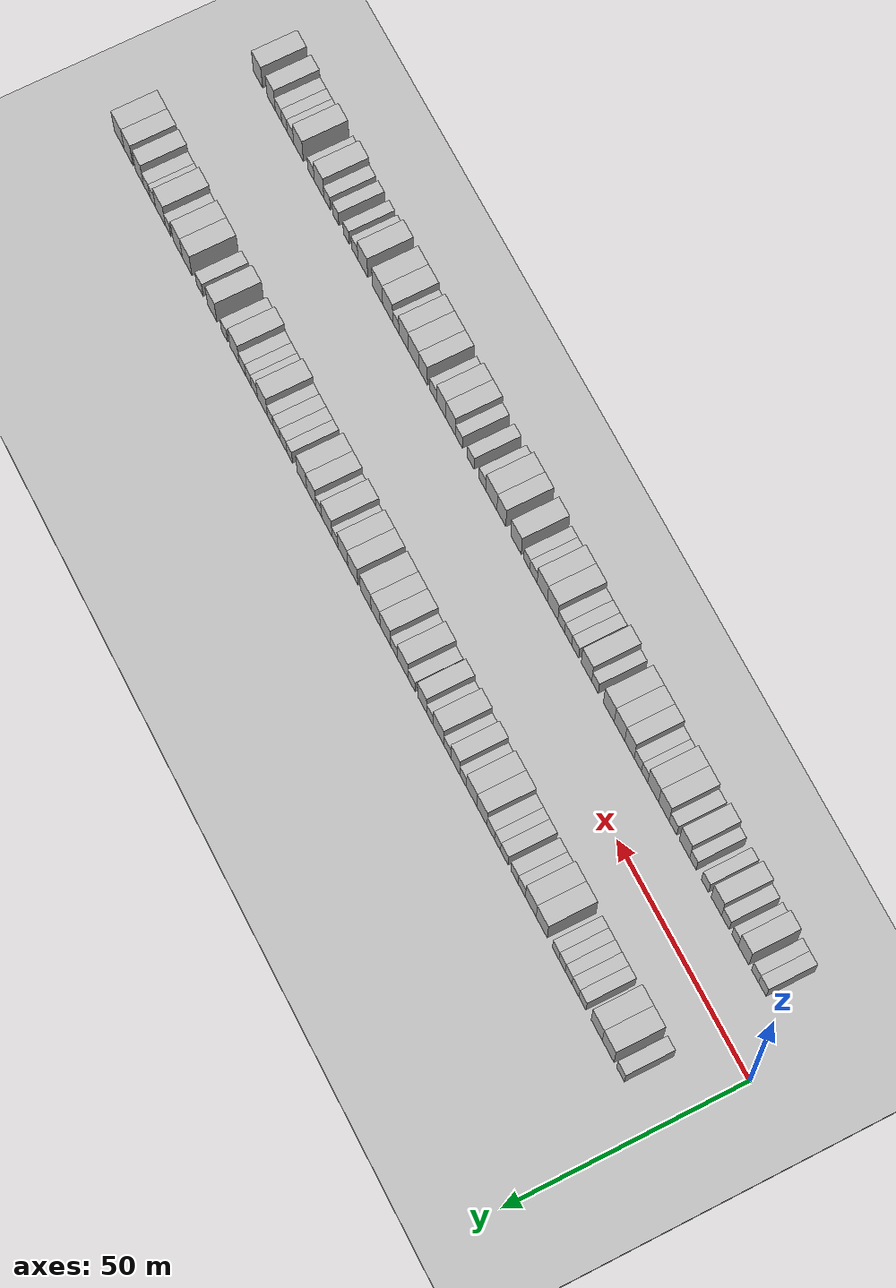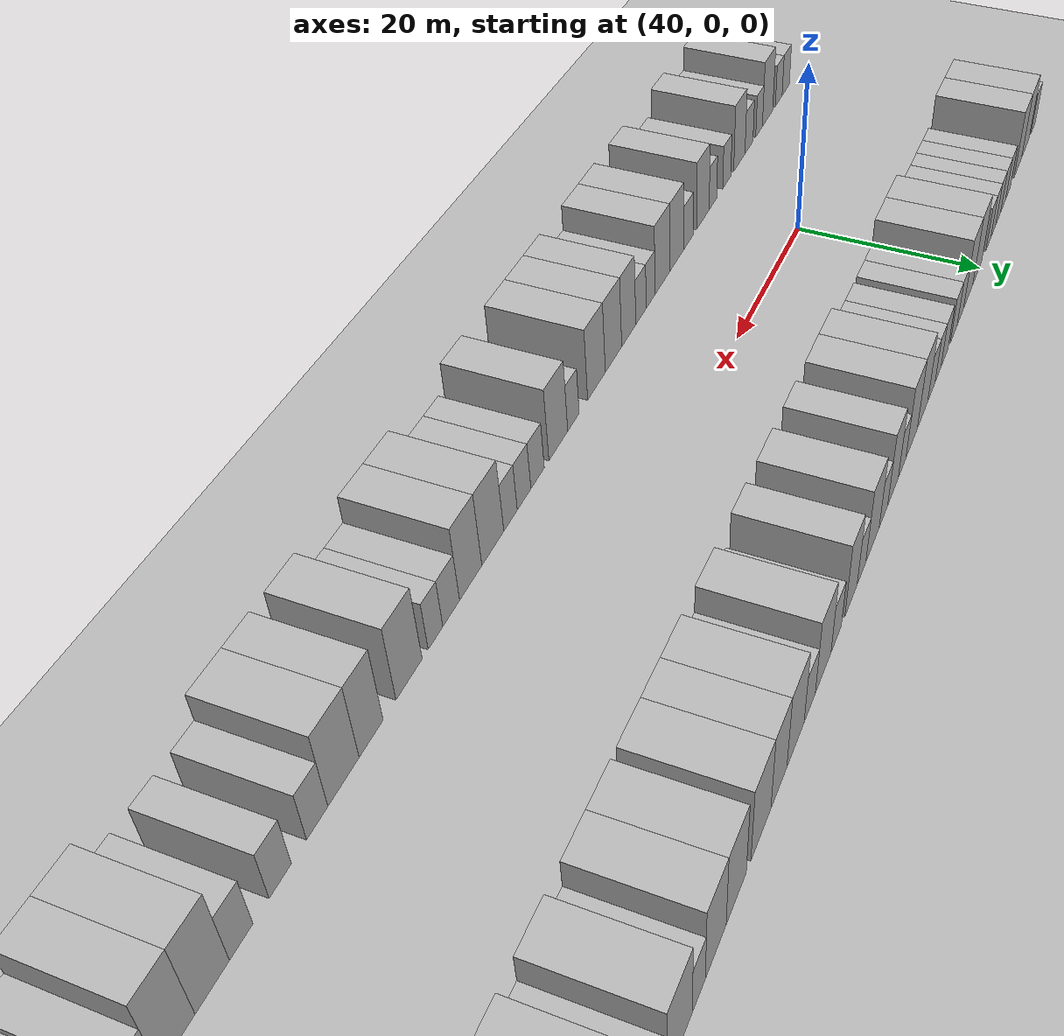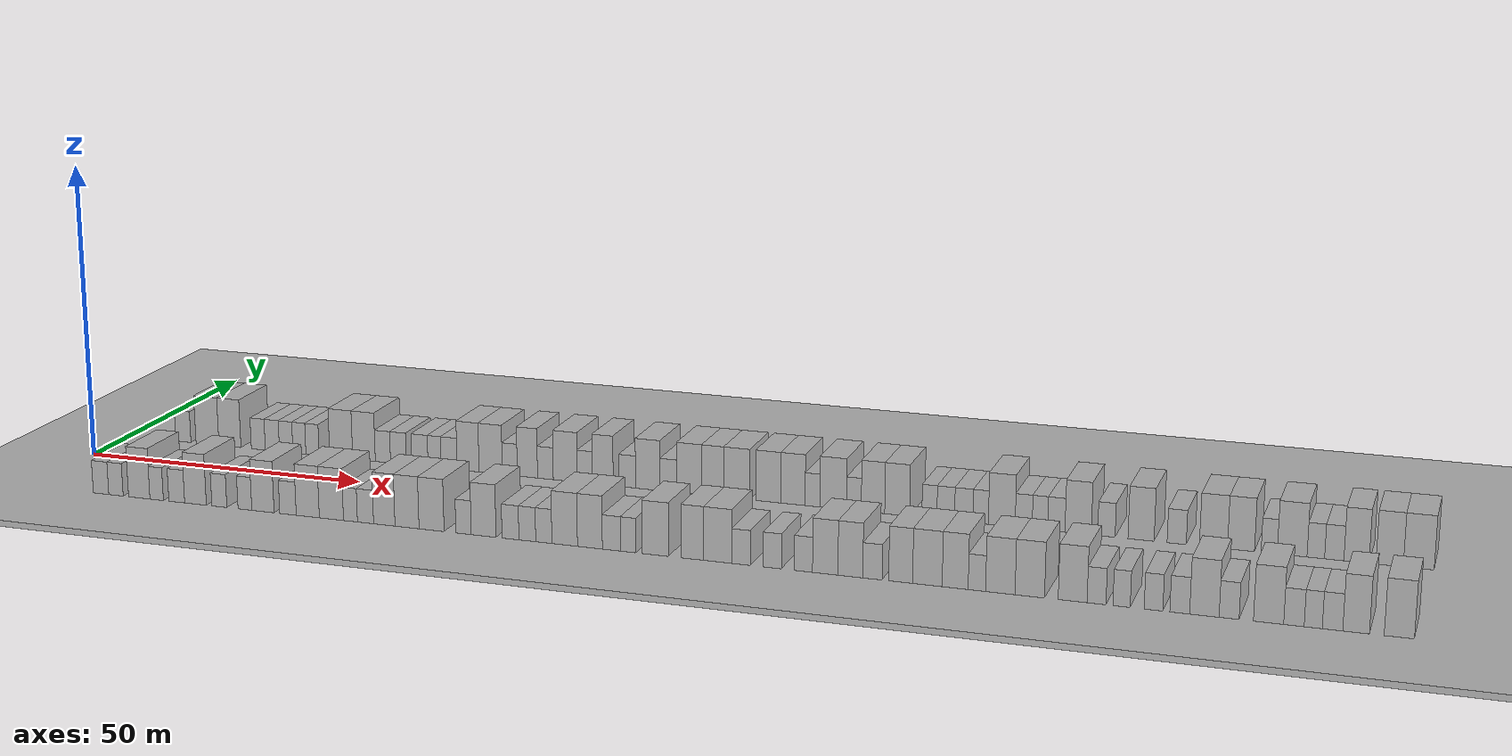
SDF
<?xml version="1.0" encoding="utf-8"?>

<sdf version="1.6">

   <world name="default">

      <gui fullscreen="0">

         <camera name="user_camera">

            <pose>-15 0 4.57585 0 0 0</pose>

            <view_controller>orbit</view_controller>

         </camera>

      </gui>

      <scene>

         <sky>

           <clouds>

             <speed>12</speed>

           </clouds>

         </sky>

         <ambient>0.4 0.4 0.4 1</ambient>

         <background>0.7 0.7 0.7 1</background>

         <shadows>1</shadows>

      </scene>

      <gravity>0 0 -9.8066</gravity>

      <magnetic_field>6e-06 2.3e-05 -4.2e-05</magnetic_field>

      <physics default="0" name="default_physics" type="ode">

         <ode>

            <solver>

               <type>quick</type>

               <iters>10</iters>

               <sor>1.0</sor>

               <use_dynamic_moi_rescaling>0</use_dynamic_moi_rescaling>

            </solver>

            <constraints>

               <cfm>0</cfm>

               <erp>0.2</erp>

               <contact_max_correcting_vel>100</contact_max_correcting_vel>

               <contact_surface_layer>0.001</contact_surface_layer>

            </constraints>

         </ode>

         <max_step_size>0.004</max_step_size>

         <real_time_factor>1</real_time_factor>

         <real_time_update_rate>250</real_time_update_rate>

      </physics>

      <light name="sun" type="directional">

         <cast_shadows>1</cast_shadows>

         <pose>0 0 10 0 0 0</pose>

         <diffuse>0.8 0.8 0.8 1</diffuse>

         <specular>0.2 0.2 0.2 1</specular>

         <attenuation>

            <range>1000</range>

            <constant>0.9</constant>

            <linear>0.01</linear>

            <quadratic>0.001</quadratic>

         </attenuation>

         <direction>-0.5 0.1 -0.9</direction>

      </light>

      <include>

         <name>ground_plane_1</name>

         <uri>model://HANNAS_ground_plane</uri>

         <pose>0 0 0  0 0 0</pose>

      </include>

      <include>

         <name>ground_plane_2</name>

         <uri>model://HANNAS_ground_plane</uri>

         <pose>100 0 0  0 0 0</pose>

      </include>

      <model name="building_1">

         <static>1</static>

         <pose frame="">11.4720 15.0000 0 0.000000 0.000000 1.570796</pose>

         <link name="link">

            <pose frame="">0 0 3.00 0 0 0</pose>

            <collision name="collision">

               <geometry>

                  <box>

                     <size>10.0000 2.9440 6.0000</size>

                  </box>

               </geometry>

               <max_contacts>10</max_contacts>

               <surface>

                  <contact>

                     <ode/>

                  </contact>

                  <bounce/>

                  <friction>

                     <torsional>

                        <ode/>

                     </torsional>

                     <ode/>

                  </friction>

               </surface>

            </collision>

            <visual name="visual">

               <cast_shadows>0</cast_shadows>

               <geometry>

                  <box>

                     <size>10.0000 2.9440 6.0000</size>

                  </box>

               </geometry>

               <material>

                  <script>

                     <uri>model://HANNAS_wall/materials/scripts</uri>

                     <uri>model://HANNAS_wall/materials/textures</uri>

                     <name>vrc/HANNAS_wall</name>

                  </script>

               </material>

            </visual>

            <self_collide>0</self_collide>

            <enable_wind>0</enable_wind>

            <kinematic>0</kinematic>

         </link>

      </model>

      <model name="building_2">

         <static>1</static>

         <pose frame="">16.1658 15.0000 0 0.000000 0.000000 1.570796</pose>

         <link name="link">

            <pose frame="">0 0 4.50 0 0 0</pose>

            <collision name="collision">

               <geometry>

                  <box>

                     <size>10.0000 4.4437 9.0000</size>

                  </box>

               </geometry>

               <max_contacts>10</max_contacts>

               <surface>

                  <contact>

                     <ode/>

                  </contact>

                  <bounce/>

                  <friction>

                     <torsional>

                        <ode/>

                     </torsional>

                     <ode/>

                  </friction>

               </surface>

            </collision>

            <visual name="visual">

               <cast_shadows>0</cast_shadows>

               <geometry>

                  <box>

                     <size>10.0000 4.4437 9.0000</size>

                  </box>

               </geometry>

               <material>

                  <script>

                     <uri>model://HANNAS_wall/materials/scripts</uri>

                     <uri>model://HANNAS_wall/materials/textures</uri>

                     <name>vrc/HANNAS_wall</name>

                  </script>

               </material>

            </visual>

            <self_collide>0</self_collide>

            <enable_wind>0</enable_wind>

            <kinematic>0</kinematic>

         </link>

      </model>

      <model name="building_3">

         <static>1</static>

         <pose frame="">20.5180 15.0000 0 0.000000 0.000000 1.570796</pose>

         <link name="link">

            <pose frame="">0 0 4.50 0 0 0</pose>

            <collision name="collision">

               <geometry>

                  <box>

                     <size>10.0000 4.2608 9.0000</size>

                  </box>

               </geometry>

               <max_contacts>10</max_contacts>

               <surface>

                  <contact>

                     <ode/>

                  </contact>

                  <bounce/>

                  <friction>

                     <torsional>

                        <ode/>

                     </torsional>

                     <ode/>

                  </friction>

               </surface>

            </collision>

            <visual name="visual">

               <cast_shadows>0</cast_shadows>

               <geometry>

                  <box>

                     <size>10.0000 4.2608 9.0000</size>

                  </box>

               </geometry>

               <material>

                  <script>

                     <uri>model://HANNAS_wall/materials/scripts</uri>

                     <uri>model://HANNAS_wall/materials/textures</uri>

                     <name>vrc/HANNAS_wall</name>

                  </script>

               </material>

            </visual>

            <self_collide>0</self_collide>

            <enable_wind>0</enable_wind>

            <kinematic>0</kinematic>

         </link>

      </model>

      <model name="building_4">

         <static>1</static>

         <pose frame="">25.9887 15.0000 0 0.000000 0.000000 1.570796</pose>

         <link name="link">

            <pose frame="">0 0 3.00 0 0 0</pose>

            <collision name="collision">

               <geometry>

                  <box>

                     <size>10.0000 2.6806 6.0000</size>

                  </box>

               </geometry>

               <max_contacts>10</max_contacts>

               <surface>

                  <contact>

                     <ode/>

                  </contact>

                  <bounce/>

                  <friction>

                     <torsional>

                        <ode/>

                     </torsional>

                     <ode/>

                  </friction>

               </surface>

            </collision>

            <visual name="visual">

               <cast_shadows>0</cast_shadows>

               <geometry>

                  <box>

                     <size>10.0000 2.6806 6.0000</size>

                  </box>

               </geometry>

               <material>

                  <script>

                     <uri>model://HANNAS_wall/materials/scripts</uri>

                     <uri>model://HANNAS_wall/materials/textures</uri>

                     <name>vrc/HANNAS_wall</name>

                  </script>

               </material>

            </visual>

            <self_collide>0</self_collide>

            <enable_wind>0</enable_wind>

            <kinematic>0</kinematic>

         </link>

      </model>

      <model name="building_5">

         <static>1</static>

         <pose frame="">28.6825 15.0000 0 0.000000 0.000000 1.570796</pose>

         <link name="link">

            <pose frame="">0 0 3.00 0 0 0</pose>

            <collision name="collision">

               <geometry>

                  <box>

                     <size>10.0000 2.7070 6.0000</size>

                  </box>

               </geometry>

               <max_contacts>10</max_contacts>

               <surface>

                  <contact>

                     <ode/>

                  </contact>

                  <bounce/>

                  <friction>

                     <torsional>

                        <ode/>

                     </torsional>

                     <ode/>

                  </friction>

               </surface>

            </collision>

            <visual name="visual">

               <cast_shadows>0</cast_shadows>

               <geometry>

                  <box>

                     <size>10.0000 2.7070 6.0000</size>

                  </box>

               </geometry>

               <material>

                  <script>

                     <uri>model://HANNAS_wall/materials/scripts</uri>

                     <uri>model://HANNAS_wall/materials/textures</uri>

                     <name>vrc/HANNAS_wall</name>

                  </script>

               </material>

            </visual>

            <self_collide>0</self_collide>

            <enable_wind>0</enable_wind>

            <kinematic>0</kinematic>

         </link>

      </model>

      <model name="building_6">

         <static>1</static>

         <pose frame="">31.3200 15.0000 0 0.000000 0.000000 1.570796</pose>

         <link name="link">

            <pose frame="">0 0 3.00 0 0 0</pose>

            <collision name="collision">

               <geometry>

                  <box>

                     <size>10.0000 2.5679 6.0000</size>

                  </box>

               </geometry>

               <max_contacts>10</max_contacts>

               <surface>

                  <contact>

                     <ode/>

                  </contact>

                  <bounce/>

                  <friction>

                     <torsional>

                        <ode/>

                     </torsional>

                     <ode/>

                  </friction>

               </surface>

            </collision>

            <visual name="visual">

               <cast_shadows>0</cast_shadows>

               <geometry>

                  <box>

                     <size>10.0000 2.5679 6.0000</size>

                  </box>

               </geometry>

               <material>

                  <script>

                     <uri>model://HANNAS_wall/materials/scripts</uri>

                     <uri>model://HANNAS_wall/materials/textures</uri>

                     <name>vrc/HANNAS_wall</name>

                  </script>

               </material>

            </visual>

            <self_collide>0</self_collide>

            <enable_wind>0</enable_wind>

            <kinematic>0</kinematic>

         </link>

      </model>

      <model name="building_7">

         <static>1</static>

         <pose frame="">33.8323 15.0000 0 0.000000 0.000000 1.570796</pose>

         <link name="link">

            <pose frame="">0 0 3.00 0 0 0</pose>

            <collision name="collision">

               <geometry>

                  <box>

                     <size>10.0000 2.4568 6.0000</size>

                  </box>

               </geometry>

               <max_contacts>10</max_contacts>

               <surface>

                  <contact>

                     <ode/>

                  </contact>

                  <bounce/>

                  <friction>

                     <torsional>

                        <ode/>

                     </torsional>

                     <ode/>

                  </friction>

               </surface>

            </collision>

            <visual name="visual">

               <cast_shadows>0</cast_shadows>

               <geometry>

                  <box>

                     <size>10.0000 2.4568 6.0000</size>

                  </box>

               </geometry>

               <material>

                  <script>

                     <uri>model://HANNAS_wall/materials/scripts</uri>

                     <uri>model://HANNAS_wall/materials/textures</uri>

                     <name>vrc/HANNAS_wall</name>

                  </script>

               </material>

            </visual>

            <self_collide>0</self_collide>

            <enable_wind>0</enable_wind>

            <kinematic>0</kinematic>

         </link>

      </model>

      <model name="building_8">

         <static>1</static>

         <pose frame="">36.3138 15.0000 0 0.000000 0.000000 1.570796</pose>

         <link name="link">

            <pose frame="">0 0 3.00 0 0 0</pose>

            <collision name="collision">

               <geometry>

                  <box>

                     <size>10.0000 2.5061 6.0000</size>

                  </box>

               </geometry>

               <max_contacts>10</max_contacts>

               <surface>

                  <contact>

                     <ode/>

                  </contact>

                  <bounce/>

                  <friction>

                     <torsional>

                        <ode/>

                     </torsional>

                     <ode/>

                  </friction>

               </surface>

            </collision>

            <visual name="visual">

               <cast_shadows>0</cast_shadows>

               <geometry>

                  <box>

                     <size>10.0000 2.5061 6.0000</size>

                  </box>

               </geometry>

               <material>

                  <script>

                     <uri>model://HANNAS_wall/materials/scripts</uri>

                     <uri>model://HANNAS_wall/materials/textures</uri>

                     <name>vrc/HANNAS_wall</name>

                  </script>

               </material>

            </visual>

            <self_collide>0</self_collide>

            <enable_wind>0</enable_wind>

            <kinematic>0</kinematic>

         </link>

      </model>

      <model name="building_9">

         <static>1</static>

         <pose frame="">41.7231 15.0000 0 0.000000 0.000000 1.570796</pose>

         <link name="link">

            <pose frame="">0 0 4.50 0 0 0</pose>

            <collision name="collision">

               <geometry>

                  <box>

                     <size>10.0000 4.3126 9.0000</size>

                  </box>

               </geometry>

               <max_contacts>10</max_contacts>

               <surface>

                  <contact>

                     <ode/>

                  </contact>

                  <bounce/>

                  <friction>

                     <torsional>

                        <ode/>

                     </torsional>

                     <ode/>

                  </friction>

               </surface>

            </collision>

            <visual name="visual">

               <cast_shadows>0</cast_shadows>

               <geometry>

                  <box>

                     <size>10.0000 4.3126 9.0000</size>

                  </box>

               </geometry>

               <material>

                  <script>

                     <uri>model://HANNAS_wall/materials/scripts</uri>

                     <uri>model://HANNAS_wall/materials/textures</uri>

                     <name>vrc/HANNAS_wall</name>

                  </script>

               </material>

            </visual>

            <self_collide>0</self_collide>

            <enable_wind>0</enable_wind>

            <kinematic>0</kinematic>

         </link>

      </model>

      <model name="building_10">

         <static>1</static>

         <pose frame="">45.9907 15.0000 0 0.000000 0.000000 1.570796</pose>

         <link name="link">

            <pose frame="">0 0 4.50 0 0 0</pose>

            <collision name="collision">

               <geometry>

                  <box>

                     <size>10.0000 4.2225 9.0000</size>

                  </box>

               </geometry>

               <max_contacts>10</max_contacts>

               <surface>

                  <contact>

                     <ode/>

                  </contact>

                  <bounce/>

                  <friction>

                     <torsional>

                        <ode/>

                     </torsional>

                     <ode/>

                  </friction>

               </surface>

            </collision>

            <visual name="visual">

               <cast_shadows>0</cast_shadows>

               <geometry>

                  <box>

                     <size>10.0000 4.2225 9.0000</size>

                  </box>

               </geometry>

               <material>

                  <script>

                     <uri>model://HANNAS_wall/materials/scripts</uri>

                     <uri>model://HANNAS_wall/materials/textures</uri>

                     <name>vrc/HANNAS_wall</name>

                  </script>

               </material>

            </visual>

            <self_collide>0</self_collide>

            <enable_wind>0</enable_wind>

            <kinematic>0</kinematic>

         </link>

      </model>

      <model name="building_11">

         <static>1</static>

         <pose frame="">49.5140 15.0000 0 0.000000 0.000000 1.570796</pose>

         <link name="link">

            <pose frame="">0 0 3.00 0 0 0</pose>

            <collision name="collision">

               <geometry>

                  <box>

                     <size>10.0000 2.8241 6.0000</size>

                  </box>

               </geometry>

               <max_contacts>10</max_contacts>

               <surface>

                  <contact>

                     <ode/>

                  </contact>

                  <bounce/>

                  <friction>

                     <torsional>

                        <ode/>

                     </torsional>

                     <ode/>

                  </friction>

               </surface>

            </collision>

            <visual name="visual">

               <cast_shadows>0</cast_shadows>

               <geometry>

                  <box>

                     <size>10.0000 2.8241 6.0000</size>

                  </box>

               </geometry>

               <material>

                  <script>

                     <uri>model://HANNAS_wall/materials/scripts</uri>

                     <uri>model://HANNAS_wall/materials/textures</uri>

                     <name>vrc/HANNAS_wall</name>

                  </script>

               </material>

            </visual>

            <self_collide>0</self_collide>

            <enable_wind>0</enable_wind>

            <kinematic>0</kinematic>

         </link>

      </model>

      <model name="building_12">

         <static>1</static>

         <pose frame="">52.3961 15.0000 0 0.000000 0.000000 1.570796</pose>

         <link name="link">

            <pose frame="">0 0 3.00 0 0 0</pose>

            <collision name="collision">

               <geometry>

                  <box>

                     <size>10.0000 2.9401 6.0000</size>

                  </box>

               </geometry>

               <max_contacts>10</max_contacts>

               <surface>

                  <contact>

                     <ode/>

                  </contact>

                  <bounce/>

                  <friction>

                     <torsional>

                        <ode/>

                     </torsional>

                     <ode/>

                  </friction>

               </surface>

            </collision>

            <visual name="visual">

               <cast_shadows>0</cast_shadows>

               <geometry>

                  <box>

                     <size>10.0000 2.9401 6.0000</size>

                  </box>

               </geometry>

               <material>

                  <script>

                     <uri>model://HANNAS_wall/materials/scripts</uri>

                     <uri>model://HANNAS_wall/materials/textures</uri>

                     <name>vrc/HANNAS_wall</name>

                  </script>

               </material>

            </visual>

            <self_collide>0</self_collide>

            <enable_wind>0</enable_wind>

            <kinematic>0</kinematic>

         </link>

      </model>

      <model name="building_13">

         <static>1</static>

         <pose frame="">56.3581 15.0000 0 0.000000 0.000000 1.570796</pose>

         <link name="link">

            <pose frame="">0 0 3.00 0 0 0</pose>

            <collision name="collision">

               <geometry>

                  <box>

                     <size>10.0000 2.9839 6.0000</size>

                  </box>

               </geometry>

               <max_contacts>10</max_contacts>

               <surface>

                  <contact>

                     <ode/>

                  </contact>

                  <bounce/>

                  <friction>

                     <torsional>

                        <ode/>

                     </torsional>

                     <ode/>

                  </friction>

               </surface>

            </collision>

            <visual name="visual">

               <cast_shadows>0</cast_shadows>

               <geometry>

                  <box>

                     <size>10.0000 2.9839 6.0000</size>

                  </box>

               </geometry>

               <material>

                  <script>

                     <uri>model://HANNAS_wall/materials/scripts</uri>

                     <uri>model://HANNAS_wall/materials/textures</uri>

                     <name>vrc/HANNAS_wall</name>

                  </script>

               </material>

            </visual>

            <self_collide>0</self_collide>

            <enable_wind>0</enable_wind>

            <kinematic>0</kinematic>

         </link>

      </model>

      <model name="building_14">

         <static>1</static>

         <pose frame="">59.0586 15.0000 0 0.000000 0.000000 1.570796</pose>

         <link name="link">

            <pose frame="">0 0 3.00 0 0 0</pose>

            <collision name="collision">

               <geometry>

                  <box>

                     <size>10.0000 2.4173 6.0000</size>

                  </box>

               </geometry>

               <max_contacts>10</max_contacts>

               <surface>

                  <contact>

                     <ode/>

                  </contact>

                  <bounce/>

                  <friction>

                     <torsional>

                        <ode/>

                     </torsional>

                     <ode/>

                  </friction>

               </surface>

            </collision>

            <visual name="visual">

               <cast_shadows>0</cast_shadows>

               <geometry>

                  <box>

                     <size>10.0000 2.4173 6.0000</size>

                  </box>

               </geometry>

               <material>

                  <script>

                     <uri>model://HANNAS_wall/materials/scripts</uri>

                     <uri>model://HANNAS_wall/materials/textures</uri>

                     <name>vrc/HANNAS_wall</name>

                  </script>

               </material>

            </visual>

            <self_collide>0</self_collide>

            <enable_wind>0</enable_wind>

            <kinematic>0</kinematic>

         </link>

      </model>

      <model name="building_15">

         <static>1</static>

         <pose frame="">61.7267 15.0000 0 0.000000 0.000000 1.570796</pose>

         <link name="link">

            <pose frame="">0 0 3.00 0 0 0</pose>

            <collision name="collision">

               <geometry>

                  <box>

                     <size>10.0000 2.9189 6.0000</size>

                  </box>

               </geometry>

               <max_contacts>10</max_contacts>

               <surface>

                  <contact>

                     <ode/>

                  </contact>

                  <bounce/>

                  <friction>

                     <torsional>

                        <ode/>

                     </torsional>

                     <ode/>

                  </friction>

               </surface>

            </collision>

            <visual name="visual">

               <cast_shadows>0</cast_shadows>

               <geometry>

                  <box>

                     <size>10.0000 2.9189 6.0000</size>

                  </box>

               </geometry>

               <material>

                  <script>

                     <uri>model://HANNAS_wall/materials/scripts</uri>

                     <uri>model://HANNAS_wall/materials/textures</uri>

                     <name>vrc/HANNAS_wall</name>

                  </script>

               </material>

            </visual>

            <self_collide>0</self_collide>

            <enable_wind>0</enable_wind>

            <kinematic>0</kinematic>

         </link>

      </model>

      <model name="building_16">

         <static>1</static>

         <pose frame="">65.1740 15.0000 0 0.000000 0.000000 1.570796</pose>

         <link name="link">

            <pose frame="">0 0 4.50 0 0 0</pose>

            <collision name="collision">

               <geometry>

                  <box>

                     <size>10.0000 3.9758 9.0000</size>

                  </box>

               </geometry>

               <max_contacts>10</max_contacts>

               <surface>

                  <contact>

                     <ode/>

                  </contact>

                  <bounce/>

                  <friction>

                     <torsional>

                        <ode/>

                     </torsional>

                     <ode/>

                  </friction>

               </surface>

            </collision>

            <visual name="visual">

               <cast_shadows>0</cast_shadows>

               <geometry>

                  <box>

                     <size>10.0000 3.9758 9.0000</size>

                  </box>

               </geometry>

               <material>

                  <script>

                     <uri>model://HANNAS_wall/materials/scripts</uri>

                     <uri>model://HANNAS_wall/materials/textures</uri>

                     <name>vrc/HANNAS_wall</name>

                  </script>

               </material>

            </visual>

            <self_collide>0</self_collide>

            <enable_wind>0</enable_wind>

            <kinematic>0</kinematic>

         </link>

      </model>

      <model name="building_17">

         <static>1</static>

         <pose frame="">69.2637 15.0000 0 0.000000 0.000000 1.570796</pose>

         <link name="link">

            <pose frame="">0 0 4.50 0 0 0</pose>

            <collision name="collision">

               <geometry>

                  <box>

                     <size>10.0000 4.2034 9.0000</size>

                  </box>

               </geometry>

               <max_contacts>10</max_contacts>

               <surface>

                  <contact>

                     <ode/>

                  </contact>

                  <bounce/>

                  <friction>

                     <torsional>

                        <ode/>

                     </torsional>

                     <ode/>

                  </friction>

               </surface>

            </collision>

            <visual name="visual">

               <cast_shadows>0</cast_shadows>

               <geometry>

                  <box>

                     <size>10.0000 4.2034 9.0000</size>

                  </box>

               </geometry>

               <material>

                  <script>

                     <uri>model://HANNAS_wall/materials/scripts</uri>

                     <uri>model://HANNAS_wall/materials/textures</uri>

                     <name>vrc/HANNAS_wall</name>

                  </script>

               </material>

            </visual>

            <self_collide>0</self_collide>

            <enable_wind>0</enable_wind>

            <kinematic>0</kinematic>

         </link>

      </model>

      <model name="building_18">

         <static>1</static>

         <pose frame="">72.7155 15.0000 0 0.000000 0.000000 1.570796</pose>

         <link name="link">

            <pose frame="">0 0 3.00 0 0 0</pose>

            <collision name="collision">

               <geometry>

                  <box>

                     <size>10.0000 2.7002 6.0000</size>

                  </box>

               </geometry>

               <max_contacts>10</max_contacts>

               <surface>

                  <contact>

                     <ode/>

                  </contact>

                  <bounce/>

                  <friction>

                     <torsional>

                        <ode/>

                     </torsional>

                     <ode/>

                  </friction>

               </surface>

            </collision>

            <visual name="visual">

               <cast_shadows>0</cast_shadows>

               <geometry>

                  <box>

                     <size>10.0000 2.7002 6.0000</size>

                  </box>

               </geometry>

               <material>

                  <script>

                     <uri>model://HANNAS_wall/materials/scripts</uri>

                     <uri>model://HANNAS_wall/materials/textures</uri>

                     <name>vrc/HANNAS_wall</name>

                  </script>

               </material>

            </visual>

            <self_collide>0</self_collide>

            <enable_wind>0</enable_wind>

            <kinematic>0</kinematic>

         </link>

      </model>

      <model name="building_19">

         <static>1</static>

         <pose frame="">75.8764 15.0000 0 0.000000 0.000000 1.570796</pose>

         <link name="link">

            <pose frame="">0 0 4.50 0 0 0</pose>

            <collision name="collision">

               <geometry>

                  <box>

                     <size>10.0000 3.6217 9.0000</size>

                  </box>

               </geometry>

               <max_contacts>10</max_contacts>

               <surface>

                  <contact>

                     <ode/>

                  </contact>

                  <bounce/>

                  <friction>

                     <torsional>

                        <ode/>

                     </torsional>

                     <ode/>

                  </friction>

               </surface>

            </collision>

            <visual name="visual">

               <cast_shadows>0</cast_shadows>

               <geometry>

                  <box>

                     <size>10.0000 3.6217 9.0000</size>

                  </box>

               </geometry>

               <material>

                  <script>

                     <uri>model://HANNAS_wall/materials/scripts</uri>

                     <uri>model://HANNAS_wall/materials/textures</uri>

                     <name>vrc/HANNAS_wall</name>

                  </script>

               </material>

            </visual>

            <self_collide>0</self_collide>

            <enable_wind>0</enable_wind>

            <kinematic>0</kinematic>

         </link>

      </model>

      <model name="building_20">

         <static>1</static>

         <pose frame="">79.0913 15.0000 0 0.000000 0.000000 1.570796</pose>

         <link name="link">

            <pose frame="">0 0 3.00 0 0 0</pose>

            <collision name="collision">

               <geometry>

                  <box>

                     <size>10.0000 2.8080 6.0000</size>

                  </box>

               </geometry>

               <max_contacts>10</max_contacts>

               <surface>

                  <contact>

                     <ode/>

                  </contact>

                  <bounce/>

                  <friction>

                     <torsional>

                        <ode/>

                     </torsional>

                     <ode/>

                  </friction>

               </surface>

            </collision>

            <visual name="visual">

               <cast_shadows>0</cast_shadows>

               <geometry>

                  <box>

                     <size>10.0000 2.8080 6.0000</size>

                  </box>

               </geometry>

               <material>

                  <script>

                     <uri>model://HANNAS_wall/materials/scripts</uri>

                     <uri>model://HANNAS_wall/materials/textures</uri>

                     <name>vrc/HANNAS_wall</name>

                  </script>

               </material>

            </visual>

            <self_collide>0</self_collide>

            <enable_wind>0</enable_wind>

            <kinematic>0</kinematic>

         </link>

      </model>

      <model name="building_21">

         <static>1</static>

         <pose frame="">82.6306 15.0000 0 0.000000 0.000000 1.570796</pose>

         <link name="link">

            <pose frame="">0 0 4.50 0 0 0</pose>

            <collision name="collision">

               <geometry>

                  <box>

                     <size>10.0000 4.2707 9.0000</size>

                  </box>

               </geometry>

               <max_contacts>10</max_contacts>

               <surface>

                  <contact>

                     <ode/>

                  </contact>

                  <bounce/>

                  <friction>

                     <torsional>

                        <ode/>

                     </torsional>

                     <ode/>

                  </friction>

               </surface>

            </collision>

            <visual name="visual">

               <cast_shadows>0</cast_shadows>

               <geometry>

                  <box>

                     <size>10.0000 4.2707 9.0000</size>

                  </box>

               </geometry>

               <material>

                  <script>

                     <uri>model://HANNAS_wall/materials/scripts</uri>

                     <uri>model://HANNAS_wall/materials/textures</uri>

                     <name>vrc/HANNAS_wall</name>

                  </script>

               </material>

            </visual>

            <self_collide>0</self_collide>

            <enable_wind>0</enable_wind>

            <kinematic>0</kinematic>

         </link>

      </model>

      <model name="building_22">

         <static>1</static>

         <pose frame="">86.1015 15.0000 0 0.000000 0.000000 1.570796</pose>

         <link name="link">

            <pose frame="">0 0 3.00 0 0 0</pose>

            <collision name="collision">

               <geometry>

                  <box>

                     <size>10.0000 2.6711 6.0000</size>

                  </box>

               </geometry>

               <max_contacts>10</max_contacts>

               <surface>

                  <contact>

                     <ode/>

                  </contact>

                  <bounce/>

                  <friction>

                     <torsional>

                        <ode/>

                     </torsional>

                     <ode/>

                  </friction>

               </surface>

            </collision>

            <visual name="visual">

               <cast_shadows>0</cast_shadows>

               <geometry>

                  <box>

                     <size>10.0000 2.6711 6.0000</size>

                  </box>

               </geometry>

               <material>

                  <script>

                     <uri>model://HANNAS_wall/materials/scripts</uri>

                     <uri>model://HANNAS_wall/materials/textures</uri>

                     <name>vrc/HANNAS_wall</name>

                  </script>

               </material>

            </visual>

            <self_collide>0</self_collide>

            <enable_wind>0</enable_wind>

            <kinematic>0</kinematic>

         </link>

      </model>

      <model name="building_23">

         <static>1</static>

         <pose frame="">89.2615 15.0000 0 0.000000 0.000000 1.570796</pose>

         <link name="link">

            <pose frame="">0 0 4.50 0 0 0</pose>

            <collision name="collision">

               <geometry>

                  <box>

                     <size>10.0000 3.6487 9.0000</size>

                  </box>

               </geometry>

               <max_contacts>10</max_contacts>

               <surface>

                  <contact>

                     <ode/>

                  </contact>

                  <bounce/>

                  <friction>

                     <torsional>

                        <ode/>

                     </torsional>

                     <ode/>

                  </friction>

               </surface>

            </collision>

            <visual name="visual">

               <cast_shadows>0</cast_shadows>

               <geometry>

                  <box>

                     <size>10.0000 3.6487 9.0000</size>

                  </box>

               </geometry>

               <material>

                  <script>

                     <uri>model://HANNAS_wall/materials/scripts</uri>

                     <uri>model://HANNAS_wall/materials/textures</uri>

                     <name>vrc/HANNAS_wall</name>

                  </script>

               </material>

            </visual>

            <self_collide>0</self_collide>

            <enable_wind>0</enable_wind>

            <kinematic>0</kinematic>

         </link>

      </model>

      <model name="building_24">

         <static>1</static>

         <pose frame="">93.5392 15.0000 0 0.000000 0.000000 1.570796</pose>

         <link name="link">

            <pose frame="">0 0 3.00 0 0 0</pose>

            <collision name="collision">

               <geometry>

                  <box>

                     <size>10.0000 2.9068 6.0000</size>

                  </box>

               </geometry>

               <max_contacts>10</max_contacts>

               <surface>

                  <contact>

                     <ode/>

                  </contact>

                  <bounce/>

                  <friction>

                     <torsional>

                        <ode/>

                     </torsional>

                     <ode/>

                  </friction>

               </surface>

            </collision>

            <visual name="visual">

               <cast_shadows>0</cast_shadows>

               <geometry>

                  <box>

                     <size>10.0000 2.9068 6.0000</size>

                  </box>

               </geometry>

               <material>

                  <script>

                     <uri>model://HANNAS_wall/materials/scripts</uri>

                     <uri>model://HANNAS_wall/materials/textures</uri>

                     <name>vrc/HANNAS_wall</name>

                  </script>

               </material>

            </visual>

            <self_collide>0</self_collide>

            <enable_wind>0</enable_wind>

            <kinematic>0</kinematic>

         </link>

      </model>

      <model name="building_25">

         <static>1</static>

         <pose frame="">97.1239 15.0000 0 0.000000 0.000000 1.570796</pose>

         <link name="link">

            <pose frame="">0 0 4.50 0 0 0</pose>

            <collision name="collision">

               <geometry>

                  <box>

                     <size>10.0000 4.2625 9.0000</size>

                  </box>

               </geometry>

               <max_contacts>10</max_contacts>

               <surface>

                  <contact>

                     <ode/>

                  </contact>

                  <bounce/>

                  <friction>

                     <torsional>

                        <ode/>

                     </torsional>

                     <ode/>

                  </friction>

               </surface>

            </collision>

            <visual name="visual">

               <cast_shadows>0</cast_shadows>

               <geometry>

                  <box>

                     <size>10.0000 4.2625 9.0000</size>

                  </box>

               </geometry>

               <material>

                  <script>

                     <uri>model://HANNAS_wall/materials/scripts</uri>

                     <uri>model://HANNAS_wall/materials/textures</uri>

                     <name>vrc/HANNAS_wall</name>

                  </script>

               </material>

            </visual>

            <self_collide>0</self_collide>

            <enable_wind>0</enable_wind>

            <kinematic>0</kinematic>

         </link>

      </model>

      <model name="building_26">

         <static>1</static>

         <pose frame="">100.7043 15.0000 0 0.000000 0.000000 1.570796</pose>

         <link name="link">

            <pose frame="">0 0 3.00 0 0 0</pose>

            <collision name="collision">

               <geometry>

                  <box>

                     <size>10.0000 2.8983 6.0000</size>

                  </box>

               </geometry>

               <max_contacts>10</max_contacts>

               <surface>

                  <contact>

                     <ode/>

                  </contact>

                  <bounce/>

                  <friction>

                     <torsional>

                        <ode/>

                     </torsional>

                     <ode/>

                  </friction>

               </surface>

            </collision>

            <visual name="visual">

               <cast_shadows>0</cast_shadows>

               <geometry>

                  <box>

                     <size>10.0000 2.8983 6.0000</size>

                  </box>

               </geometry>

               <material>

                  <script>

                     <uri>model://HANNAS_wall/materials/scripts</uri>

                     <uri>model://HANNAS_wall/materials/textures</uri>

                     <name>vrc/HANNAS_wall</name>

                  </script>

               </material>

            </visual>

            <self_collide>0</self_collide>

            <enable_wind>0</enable_wind>

            <kinematic>0</kinematic>

         </link>

      </model>

      <model name="building_27">

         <static>1</static>

         <pose frame="">104.2949 15.0000 0 0.000000 0.000000 1.570796</pose>

         <link name="link">

            <pose frame="">0 0 4.50 0 0 0</pose>

            <collision name="collision">

               <geometry>

                  <box>

                     <size>10.0000 4.2830 9.0000</size>

                  </box>

               </geometry>

               <max_contacts>10</max_contacts>

               <surface>

                  <contact>

                     <ode/>

                  </contact>

                  <bounce/>

                  <friction>

                     <torsional>

                        <ode/>

                     </torsional>

                     <ode/>

                  </friction>

               </surface>

            </collision>

            <visual name="visual">

               <cast_shadows>0</cast_shadows>

               <geometry>

                  <box>

                     <size>10.0000 4.2830 9.0000</size>

                  </box>

               </geometry>

               <material>

                  <script>

                     <uri>model://HANNAS_wall/materials/scripts</uri>

                     <uri>model://HANNAS_wall/materials/textures</uri>

                     <name>vrc/HANNAS_wall</name>

                  </script>

               </material>

            </visual>

            <self_collide>0</self_collide>

            <enable_wind>0</enable_wind>

            <kinematic>0</kinematic>

         </link>

      </model>

      <model name="building_28">

         <static>1</static>

         <pose frame="">108.3185 15.0000 0 0.000000 0.000000 1.570796</pose>

         <link name="link">

            <pose frame="">0 0 4.50 0 0 0</pose>

            <collision name="collision">

               <geometry>

                  <box>

                     <size>10.0000 3.7640 9.0000</size>

                  </box>

               </geometry>

               <max_contacts>10</max_contacts>

               <surface>

                  <contact>

                     <ode/>

                  </contact>

                  <bounce/>

                  <friction>

                     <torsional>

                        <ode/>

                     </torsional>

                     <ode/>

                  </friction>

               </surface>

            </collision>

            <visual name="visual">

               <cast_shadows>0</cast_shadows>

               <geometry>

                  <box>

                     <size>10.0000 3.7640 9.0000</size>

                  </box>

               </geometry>

               <material>

                  <script>

                     <uri>model://HANNAS_wall/materials/scripts</uri>

                     <uri>model://HANNAS_wall/materials/textures</uri>

                     <name>vrc/HANNAS_wall</name>

                  </script>

               </material>

            </visual>

            <self_collide>0</self_collide>

            <enable_wind>0</enable_wind>

            <kinematic>0</kinematic>

         </link>

      </model>

      <model name="building_29">

         <static>1</static>

         <pose frame="">112.4363 15.0000 0 0.000000 0.000000 1.570796</pose>

         <link name="link">

            <pose frame="">0 0 4.50 0 0 0</pose>

            <collision name="collision">

               <geometry>

                  <box>

                     <size>10.0000 4.4717 9.0000</size>

                  </box>

               </geometry>

               <max_contacts>10</max_contacts>

               <surface>

                  <contact>

                     <ode/>

                  </contact>

                  <bounce/>

                  <friction>

                     <torsional>

                        <ode/>

                     </torsional>

                     <ode/>

                  </friction>

               </surface>

            </collision>

            <visual name="visual">

               <cast_shadows>0</cast_shadows>

               <geometry>

                  <box>

                     <size>10.0000 4.4717 9.0000</size>

                  </box>

               </geometry>

               <material>

                  <script>

                     <uri>model://HANNAS_wall/materials/scripts</uri>

                     <uri>model://HANNAS_wall/materials/textures</uri>

                     <name>vrc/HANNAS_wall</name>

                  </script>

               </material>

            </visual>

            <self_collide>0</self_collide>

            <enable_wind>0</enable_wind>

            <kinematic>0</kinematic>

         </link>

      </model>

      <model name="building_30">

         <static>1</static>

         <pose frame="">117.7677 15.0000 0 0.000000 0.000000 1.570796</pose>

         <link name="link">

            <pose frame="">0 0 4.50 0 0 0</pose>

            <collision name="collision">

               <geometry>

                  <box>

                     <size>10.0000 4.1911 9.0000</size>

                  </box>

               </geometry>

               <max_contacts>10</max_contacts>

               <surface>

                  <contact>

                     <ode/>

                  </contact>

                  <bounce/>

                  <friction>

                     <torsional>

                        <ode/>

                     </torsional>

                     <ode/>

                  </friction>

               </surface>

            </collision>

            <visual name="visual">

               <cast_shadows>0</cast_shadows>

               <geometry>

                  <box>

                     <size>10.0000 4.1911 9.0000</size>

                  </box>

               </geometry>

               <material>

                  <script>

                     <uri>model://HANNAS_wall/materials/scripts</uri>

                     <uri>model://HANNAS_wall/materials/textures</uri>

                     <name>vrc/HANNAS_wall</name>

                  </script>

               </material>

            </visual>

            <self_collide>0</self_collide>

            <enable_wind>0</enable_wind>

            <kinematic>0</kinematic>

         </link>

      </model>

      <model name="building_31">

         <static>1</static>

         <pose frame="">121.9125 15.0000 0 0.000000 0.000000 1.570796</pose>

         <link name="link">

            <pose frame="">0 0 4.50 0 0 0</pose>

            <collision name="collision">

               <geometry>

                  <box>

                     <size>10.0000 4.0984 9.0000</size>

                  </box>

               </geometry>

               <max_contacts>10</max_contacts>

               <surface>

                  <contact>

                     <ode/>

                  </contact>

                  <bounce/>

                  <friction>

                     <torsional>

                        <ode/>

                     </torsional>

                     <ode/>

                  </friction>

               </surface>

            </collision>

            <visual name="visual">

               <cast_shadows>0</cast_shadows>

               <geometry>

                  <box>

                     <size>10.0000 4.0984 9.0000</size>

                  </box>

               </geometry>

               <material>

                  <script>

                     <uri>model://HANNAS_wall/materials/scripts</uri>

                     <uri>model://HANNAS_wall/materials/textures</uri>

                     <name>vrc/HANNAS_wall</name>

                  </script>

               </material>

            </visual>

            <self_collide>0</self_collide>

            <enable_wind>0</enable_wind>

            <kinematic>0</kinematic>

         </link>

      </model>

      <model name="building_32">

         <static>1</static>

         <pose frame="">125.1835 15.0000 0 0.000000 0.000000 1.570796</pose>

         <link name="link">

            <pose frame="">0 0 3.00 0 0 0</pose>

            <collision name="collision">

               <geometry>

                  <box>

                     <size>10.0000 2.4436 6.0000</size>

                  </box>

               </geometry>

               <max_contacts>10</max_contacts>

               <surface>

                  <contact>

                     <ode/>

                  </contact>

                  <bounce/>

                  <friction>

                     <torsional>

                        <ode/>

                     </torsional>

                     <ode/>

                  </friction>

               </surface>

            </collision>

            <visual name="visual">

               <cast_shadows>0</cast_shadows>

               <geometry>

                  <box>

                     <size>10.0000 2.4436 6.0000</size>

                  </box>

               </geometry>

               <material>

                  <script>

                     <uri>model://HANNAS_wall/materials/scripts</uri>

                     <uri>model://HANNAS_wall/materials/textures</uri>

                     <name>vrc/HANNAS_wall</name>

                  </script>

               </material>

            </visual>

            <self_collide>0</self_collide>

            <enable_wind>0</enable_wind>

            <kinematic>0</kinematic>

         </link>

      </model>

      <model name="building_33">

         <static>1</static>

         <pose frame="">128.6230 15.0000 0 0.000000 0.000000 1.570796</pose>

         <link name="link">

            <pose frame="">0 0 4.50 0 0 0</pose>

            <collision name="collision">

               <geometry>

                  <box>

                     <size>10.0000 4.4353 9.0000</size>

                  </box>

               </geometry>

               <max_contacts>10</max_contacts>

               <surface>

                  <contact>

                     <ode/>

                  </contact>

                  <bounce/>

                  <friction>

                     <torsional>

                        <ode/>

                     </torsional>

                     <ode/>

                  </friction>

               </surface>

            </collision>

            <visual name="visual">

               <cast_shadows>0</cast_shadows>

               <geometry>

                  <box>

                     <size>10.0000 4.4353 9.0000</size>

                  </box>

               </geometry>

               <material>

                  <script>

                     <uri>model://HANNAS_wall/materials/scripts</uri>

                     <uri>model://HANNAS_wall/materials/textures</uri>

                     <name>vrc/HANNAS_wall</name>

                  </script>

               </material>

            </visual>

            <self_collide>0</self_collide>

            <enable_wind>0</enable_wind>

            <kinematic>0</kinematic>

         </link>

      </model>

      <model name="building_34">

         <static>1</static>

         <pose frame="">132.0591 15.0000 0 0.000000 0.000000 1.570796</pose>

         <link name="link">

            <pose frame="">0 0 3.00 0 0 0</pose>

            <collision name="collision">

               <geometry>

                  <box>

                     <size>10.0000 2.4370 6.0000</size>

                  </box>

               </geometry>

               <max_contacts>10</max_contacts>

               <surface>

                  <contact>

                     <ode/>

                  </contact>

                  <bounce/>

                  <friction>

                     <torsional>

                        <ode/>

                     </torsional>

                     <ode/>

                  </friction>

               </surface>

            </collision>

            <visual name="visual">

               <cast_shadows>0</cast_shadows>

               <geometry>

                  <box>

                     <size>10.0000 2.4370 6.0000</size>

                  </box>

               </geometry>

               <material>

                  <script>

                     <uri>model://HANNAS_wall/materials/scripts</uri>

                     <uri>model://HANNAS_wall/materials/textures</uri>

                     <name>vrc/HANNAS_wall</name>

                  </script>

               </material>

            </visual>

            <self_collide>0</self_collide>

            <enable_wind>0</enable_wind>

            <kinematic>0</kinematic>

         </link>

      </model>

      <model name="building_35">

         <static>1</static>

         <pose frame="">135.2093 15.0000 0 0.000000 0.000000 1.570796</pose>

         <link name="link">

            <pose frame="">0 0 4.50 0 0 0</pose>

            <collision name="collision">

               <geometry>

                  <box>

                     <size>10.0000 3.8633 9.0000</size>

                  </box>

               </geometry>

               <max_contacts>10</max_contacts>

               <surface>

                  <contact>

                     <ode/>

                  </contact>

                  <bounce/>

                  <friction>

                     <torsional>

                        <ode/>

                     </torsional>

                     <ode/>

                  </friction>

               </surface>

            </collision>

            <visual name="visual">

               <cast_shadows>0</cast_shadows>

               <geometry>

                  <box>

                     <size>10.0000 3.8633 9.0000</size>

                  </box>

               </geometry>

               <material>

                  <script>

                     <uri>model://HANNAS_wall/materials/scripts</uri>

                     <uri>model://HANNAS_wall/materials/textures</uri>

                     <name>vrc/HANNAS_wall</name>

                  </script>

               </material>

            </visual>

            <self_collide>0</self_collide>

            <enable_wind>0</enable_wind>

            <kinematic>0</kinematic>

         </link>

      </model>

      <model name="building_36">

         <static>1</static>

         <pose frame="">139.1776 15.0000 0 0.000000 0.000000 1.570796</pose>

         <link name="link">

            <pose frame="">0 0 4.50 0 0 0</pose>

            <collision name="collision">

               <geometry>

                  <box>

                     <size>10.0000 4.0733 9.0000</size>

                  </box>

               </geometry>

               <max_contacts>10</max_contacts>

               <surface>

                  <contact>

                     <ode/>

                  </contact>

                  <bounce/>

                  <friction>

                     <torsional>

                        <ode/>

                     </torsional>

                     <ode/>

                  </friction>

               </surface>

            </collision>

            <visual name="visual">

               <cast_shadows>0</cast_shadows>

               <geometry>

                  <box>

                     <size>10.0000 4.0733 9.0000</size>

                  </box>

               </geometry>

               <material>

                  <script>

                     <uri>model://HANNAS_wall/materials/scripts</uri>

                     <uri>model://HANNAS_wall/materials/textures</uri>

                     <name>vrc/HANNAS_wall</name>

                  </script>

               </material>

            </visual>

            <self_collide>0</self_collide>

            <enable_wind>0</enable_wind>

            <kinematic>0</kinematic>

         </link>

      </model>

      <model name="building_37">

         <static>1</static>

         <pose frame="">144.4337 15.0000 0 0.000000 0.000000 1.570796</pose>

         <link name="link">

            <pose frame="">0 0 3.00 0 0 0</pose>

            <collision name="collision">

               <geometry>

                  <box>

                     <size>10.0000 2.4388 6.0000</size>

                  </box>

               </geometry>

               <max_contacts>10</max_contacts>

               <surface>

                  <contact>

                     <ode/>

                  </contact>

                  <bounce/>

                  <friction>

                     <torsional>

                        <ode/>

                     </torsional>

                     <ode/>

                  </friction>

               </surface>

            </collision>

            <visual name="visual">

               <cast_shadows>0</cast_shadows>

               <geometry>

                  <box>

                     <size>10.0000 2.4388 6.0000</size>

                  </box>

               </geometry>

               <material>

                  <script>

                     <uri>model://HANNAS_wall/materials/scripts</uri>

                     <uri>model://HANNAS_wall/materials/textures</uri>

                     <name>vrc/HANNAS_wall</name>

                  </script>

               </material>

            </visual>

            <self_collide>0</self_collide>

            <enable_wind>0</enable_wind>

            <kinematic>0</kinematic>

         </link>

      </model>

      <model name="building_38">

         <static>1</static>

         <pose frame="">147.0817 15.0000 0 0.000000 0.000000 1.570796</pose>

         <link name="link">

            <pose frame="">0 0 3.00 0 0 0</pose>

            <collision name="collision">

               <geometry>

                  <box>

                     <size>10.0000 2.8573 6.0000</size>

                  </box>

               </geometry>

               <max_contacts>10</max_contacts>

               <surface>

                  <contact>

                     <ode/>

                  </contact>

                  <bounce/>

                  <friction>

                     <torsional>

                        <ode/>

                     </torsional>

                     <ode/>

                  </friction>

               </surface>

            </collision>

            <visual name="visual">

               <cast_shadows>0</cast_shadows>

               <geometry>

                  <box>

                     <size>10.0000 2.8573 6.0000</size>

                  </box>

               </geometry>

               <material>

                  <script>

                     <uri>model://HANNAS_wall/materials/scripts</uri>

                     <uri>model://HANNAS_wall/materials/textures</uri>

                     <name>vrc/HANNAS_wall</name>

                  </script>

               </material>

            </visual>

            <self_collide>0</self_collide>

            <enable_wind>0</enable_wind>

            <kinematic>0</kinematic>

         </link>

      </model>

      <model name="building_39">

         <static>1</static>

         <pose frame="">149.9892 15.0000 0 0.000000 0.000000 1.570796</pose>

         <link name="link">

            <pose frame="">0 0 3.00 0 0 0</pose>

            <collision name="collision">

               <geometry>

                  <box>

                     <size>10.0000 2.9577 6.0000</size>

                  </box>

               </geometry>

               <max_contacts>10</max_contacts>

               <surface>

                  <contact>

                     <ode/>

                  </contact>

                  <bounce/>

                  <friction>

                     <torsional>

                        <ode/>

                     </torsional>

                     <ode/>

                  </friction>

               </surface>

            </collision>

            <visual name="visual">

               <cast_shadows>0</cast_shadows>

               <geometry>

                  <box>

                     <size>10.0000 2.9577 6.0000</size>

                  </box>

               </geometry>

               <material>

                  <script>

                     <uri>model://HANNAS_wall/materials/scripts</uri>

                     <uri>model://HANNAS_wall/materials/textures</uri>

                     <name>vrc/HANNAS_wall</name>

                  </script>

               </material>

            </visual>

            <self_collide>0</self_collide>

            <enable_wind>0</enable_wind>

            <kinematic>0</kinematic>

         </link>

      </model>

      <model name="building_40">

         <static>1</static>

         <pose frame="">152.7050 15.0000 0 0.000000 0.000000 1.570796</pose>

         <link name="link">

            <pose frame="">0 0 3.00 0 0 0</pose>

            <collision name="collision">

               <geometry>

                  <box>

                     <size>10.0000 2.4739 6.0000</size>

                  </box>

               </geometry>

               <max_contacts>10</max_contacts>

               <surface>

                  <contact>

                     <ode/>

                  </contact>

                  <bounce/>

                  <friction>

                     <torsional>

                        <ode/>

                     </torsional>

                     <ode/>

                  </friction>

               </surface>

            </collision>

            <visual name="visual">

               <cast_shadows>0</cast_shadows>

               <geometry>

                  <box>

                     <size>10.0000 2.4739 6.0000</size>

                  </box>

               </geometry>

               <material>

                  <script>

                     <uri>model://HANNAS_wall/materials/scripts</uri>

                     <uri>model://HANNAS_wall/materials/textures</uri>

                     <name>vrc/HANNAS_wall</name>

                  </script>

               </material>

            </visual>

            <self_collide>0</self_collide>

            <enable_wind>0</enable_wind>

            <kinematic>0</kinematic>

         </link>

      </model>

      <model name="building_41">

         <static>1</static>

         <pose frame="">156.0827 15.0000 0 0.000000 0.000000 1.570796</pose>

         <link name="link">

            <pose frame="">0 0 4.50 0 0 0</pose>

            <collision name="collision">

               <geometry>

                  <box>

                     <size>10.0000 4.2815 9.0000</size>

                  </box>

               </geometry>

               <max_contacts>10</max_contacts>

               <surface>

                  <contact>

                     <ode/>

                  </contact>

                  <bounce/>

                  <friction>

                     <torsional>

                        <ode/>

                     </torsional>

                     <ode/>

                  </friction>

               </surface>

            </collision>

            <visual name="visual">

               <cast_shadows>0</cast_shadows>

               <geometry>

                  <box>

                     <size>10.0000 4.2815 9.0000</size>

                  </box>

               </geometry>

               <material>

                  <script>

                     <uri>model://HANNAS_wall/materials/scripts</uri>

                     <uri>model://HANNAS_wall/materials/textures</uri>

                     <name>vrc/HANNAS_wall</name>

                  </script>

               </material>

            </visual>

            <self_collide>0</self_collide>

            <enable_wind>0</enable_wind>

            <kinematic>0</kinematic>

         </link>

      </model>

      <model name="building_42">

         <static>1</static>

         <pose frame="">159.5707 15.0000 0 0.000000 0.000000 1.570796</pose>

         <link name="link">

            <pose frame="">0 0 3.00 0 0 0</pose>

            <collision name="collision">

               <geometry>

                  <box>

                     <size>10.0000 2.6945 6.0000</size>

                  </box>

               </geometry>

               <max_contacts>10</max_contacts>

               <surface>

                  <contact>

                     <ode/>

                  </contact>

                  <bounce/>

                  <friction>

                     <torsional>

                        <ode/>

                     </torsional>

                     <ode/>

                  </friction>

               </surface>

            </collision>

            <visual name="visual">

               <cast_shadows>0</cast_shadows>

               <geometry>

                  <box>

                     <size>10.0000 2.6945 6.0000</size>

                  </box>

               </geometry>

               <material>

                  <script>

                     <uri>model://HANNAS_wall/materials/scripts</uri>

                     <uri>model://HANNAS_wall/materials/textures</uri>

                     <name>vrc/HANNAS_wall</name>

                  </script>

               </material>

            </visual>

            <self_collide>0</self_collide>

            <enable_wind>0</enable_wind>

            <kinematic>0</kinematic>

         </link>

      </model>

      <model name="building_43">

         <static>1</static>

         <pose frame="">162.1420 15.0000 0 0.000000 0.000000 1.570796</pose>

         <link name="link">

            <pose frame="">0 0 3.00 0 0 0</pose>

            <collision name="collision">

               <geometry>

                  <box>

                     <size>10.0000 2.4482 6.0000</size>

                  </box>

               </geometry>

               <max_contacts>10</max_contacts>

               <surface>

                  <contact>

                     <ode/>

                  </contact>

                  <bounce/>

                  <friction>

                     <torsional>

                        <ode/>

                     </torsional>

                     <ode/>

                  </friction>

               </surface>

            </collision>

            <visual name="visual">

               <cast_shadows>0</cast_shadows>

               <geometry>

                  <box>

                     <size>10.0000 2.4482 6.0000</size>

                  </box>

               </geometry>

               <material>

                  <script>

                     <uri>model://HANNAS_wall/materials/scripts</uri>

                     <uri>model://HANNAS_wall/materials/textures</uri>

                     <name>vrc/HANNAS_wall</name>

                  </script>

               </material>

            </visual>

            <self_collide>0</self_collide>

            <enable_wind>0</enable_wind>

            <kinematic>0</kinematic>

         </link>

      </model>

      <model name="building_44">

         <static>1</static>

         <pose frame="">164.7349 15.0000 0 0.000000 0.000000 1.570796</pose>

         <link name="link">

            <pose frame="">0 0 3.00 0 0 0</pose>

            <collision name="collision">

               <geometry>

                  <box>

                     <size>10.0000 2.7376 6.0000</size>

                  </box>

               </geometry>

               <max_contacts>10</max_contacts>

               <surface>

                  <contact>

                     <ode/>

                  </contact>

                  <bounce/>

                  <friction>

                     <torsional>

                        <ode/>

                     </torsional>

                     <ode/>

                  </friction>

               </surface>

            </collision>

            <visual name="visual">

               <cast_shadows>0</cast_shadows>

               <geometry>

                  <box>

                     <size>10.0000 2.7376 6.0000</size>

                  </box>

               </geometry>

               <material>

                  <script>

                     <uri>model://HANNAS_wall/materials/scripts</uri>

                     <uri>model://HANNAS_wall/materials/textures</uri>

                     <name>vrc/HANNAS_wall</name>

                  </script>

               </material>

            </visual>

            <self_collide>0</self_collide>

            <enable_wind>0</enable_wind>

            <kinematic>0</kinematic>

         </link>

      </model>

      <model name="building_45">

         <static>1</static>

         <pose frame="">168.1659 15.0000 0 0.000000 0.000000 1.570796</pose>

         <link name="link">

            <pose frame="">0 0 4.50 0 0 0</pose>

            <collision name="collision">

               <geometry>

                  <box>

                     <size>10.0000 4.1245 9.0000</size>

                  </box>

               </geometry>

               <max_contacts>10</max_contacts>

               <surface>

                  <contact>

                     <ode/>

                  </contact>

                  <bounce/>

                  <friction>

                     <torsional>

                        <ode/>

                     </torsional>

                     <ode/>

                  </friction>

               </surface>

            </collision>

            <visual name="visual">

               <cast_shadows>0</cast_shadows>

               <geometry>

                  <box>

                     <size>10.0000 4.1245 9.0000</size>

                  </box>

               </geometry>

               <material>

                  <script>

                     <uri>model://HANNAS_wall/materials/scripts</uri>

                     <uri>model://HANNAS_wall/materials/textures</uri>

                     <name>vrc/HANNAS_wall</name>

                  </script>

               </material>

            </visual>

            <self_collide>0</self_collide>

            <enable_wind>0</enable_wind>

            <kinematic>0</kinematic>

         </link>

      </model>

      <model name="building_46">

         <static>1</static>

         <pose frame="">172.5894 15.0000 0 0.000000 0.000000 1.570796</pose>

         <link name="link">

            <pose frame="">0 0 3.00 0 0 0</pose>

            <collision name="collision">

               <geometry>

                  <box>

                     <size>10.0000 2.7224 6.0000</size>

                  </box>

               </geometry>

               <max_contacts>10</max_contacts>

               <surface>

                  <contact>

                     <ode/>

                  </contact>

                  <bounce/>

                  <friction>

                     <torsional>

                        <ode/>

                     </torsional>

                     <ode/>

                  </friction>

               </surface>

            </collision>

            <visual name="visual">

               <cast_shadows>0</cast_shadows>

               <geometry>

                  <box>

                     <size>10.0000 2.7224 6.0000</size>

                  </box>

               </geometry>

               <material>

                  <script>

                     <uri>model://HANNAS_wall/materials/scripts</uri>

                     <uri>model://HANNAS_wall/materials/textures</uri>

                     <name>vrc/HANNAS_wall</name>

                  </script>

               </material>

            </visual>

            <self_collide>0</self_collide>

            <enable_wind>0</enable_wind>

            <kinematic>0</kinematic>

         </link>

      </model>

      <model name="building_47">

         <static>1</static>

         <pose frame="">177.9685 15.0000 0 0.000000 0.000000 1.570796</pose>

         <link name="link">

            <pose frame="">0 0 4.50 0 0 0</pose>

            <collision name="collision">

               <geometry>

                  <box>

                     <size>10.0000 4.0358 9.0000</size>

                  </box>

               </geometry>

               <max_contacts>10</max_contacts>

               <surface>

                  <contact>

                     <ode/>

                  </contact>

                  <bounce/>

                  <friction>

                     <torsional>

                        <ode/>

                     </torsional>

                     <ode/>

                  </friction>

               </surface>

            </collision>

            <visual name="visual">

               <cast_shadows>0</cast_shadows>

               <geometry>

                  <box>

                     <size>10.0000 4.0358 9.0000</size>

                  </box>

               </geometry>

               <material>

                  <script>

                     <uri>model://HANNAS_wall/materials/scripts</uri>

                     <uri>model://HANNAS_wall/materials/textures</uri>

                     <name>vrc/HANNAS_wall</name>

                  </script>

               </material>

            </visual>

            <self_collide>0</self_collide>

            <enable_wind>0</enable_wind>

            <kinematic>0</kinematic>

         </link>

      </model>

      <model name="building_48">

         <static>1</static>

         <pose frame="">183.4565 15.0000 0 0.000000 0.000000 1.570796</pose>

         <link name="link">

            <pose frame="">0 0 3.00 0 0 0</pose>

            <collision name="collision">

               <geometry>

                  <box>

                     <size>10.0000 2.9402 6.0000</size>

                  </box>

               </geometry>

               <max_contacts>10</max_contacts>

               <surface>

                  <contact>

                     <ode/>

                  </contact>

                  <bounce/>

                  <friction>

                     <torsional>

                        <ode/>

                     </torsional>

                     <ode/>

                  </friction>

               </surface>

            </collision>

            <visual name="visual">

               <cast_shadows>0</cast_shadows>

               <geometry>

                  <box>

                     <size>10.0000 2.9402 6.0000</size>

                  </box>

               </geometry>

               <material>

                  <script>

                     <uri>model://HANNAS_wall/materials/scripts</uri>

                     <uri>model://HANNAS_wall/materials/textures</uri>

                     <name>vrc/HANNAS_wall</name>

                  </script>

               </material>

            </visual>

            <self_collide>0</self_collide>

            <enable_wind>0</enable_wind>

            <kinematic>0</kinematic>

         </link>

      </model>

      <model name="building_49">

         <static>1</static>

         <pose frame="">189.0600 15.0000 0 0.000000 0.000000 1.570796</pose>

         <link name="link">

            <pose frame="">0 0 4.50 0 0 0</pose>

            <collision name="collision">

               <geometry>

                  <box>

                     <size>10.0000 4.2668 9.0000</size>

                  </box>

               </geometry>

               <max_contacts>10</max_contacts>

               <surface>

                  <contact>

                     <ode/>

                  </contact>

                  <bounce/>

                  <friction>

                     <torsional>

                        <ode/>

                     </torsional>

                     <ode/>

                  </friction>

               </surface>

            </collision>

            <visual name="visual">

               <cast_shadows>0</cast_shadows>

               <geometry>

                  <box>

                     <size>10.0000 4.2668 9.0000</size>

                  </box>

               </geometry>

               <material>

                  <script>

                     <uri>model://HANNAS_wall/materials/scripts</uri>

                     <uri>model://HANNAS_wall/materials/textures</uri>

                     <name>vrc/HANNAS_wall</name>

                  </script>

               </material>

            </visual>

            <self_collide>0</self_collide>

            <enable_wind>0</enable_wind>

            <kinematic>0</kinematic>

         </link>

      </model>

      <model name="building_50">

         <static>1</static>

         <pose frame="">193.2329 15.0000 0 0.000000 0.000000 1.570796</pose>

         <link name="link">

            <pose frame="">0 0 4.50 0 0 0</pose>

            <collision name="collision">

               <geometry>

                  <box>

                     <size>10.0000 4.0790 9.0000</size>

                  </box>

               </geometry>

               <max_contacts>10</max_contacts>

               <surface>

                  <contact>

                     <ode/>

                  </contact>

                  <bounce/>

                  <friction>

                     <torsional>

                        <ode/>

                     </torsional>

                     <ode/>

                  </friction>

               </surface>

            </collision>

            <visual name="visual">

               <cast_shadows>0</cast_shadows>

               <geometry>

                  <box>

                     <size>10.0000 4.0790 9.0000</size>

                  </box>

               </geometry>

               <material>

                  <script>

                     <uri>model://HANNAS_wall/materials/scripts</uri>

                     <uri>model://HANNAS_wall/materials/textures</uri>

                     <name>vrc/HANNAS_wall</name>

                  </script>

               </material>

            </visual>

            <self_collide>0</self_collide>

            <enable_wind>0</enable_wind>

            <kinematic>0</kinematic>

         </link>

      </model>

      <model name="building_51">

         <static>1</static>

         <pose frame="">197.4810 15.0000 0 0.000000 0.000000 1.570796</pose>

         <link name="link">

            <pose frame="">0 0 3.00 0 0 0</pose>

            <collision name="collision">

               <geometry>

                  <box>

                     <size>10.0000 2.4172 6.0000</size>

                  </box>

               </geometry>

               <max_contacts>10</max_contacts>

               <surface>

                  <contact>

                     <ode/>

                  </contact>

                  <bounce/>

                  <friction>

                     <torsional>

                        <ode/>

                     </torsional>

                     <ode/>

                  </friction>

               </surface>

            </collision>

            <visual name="visual">

               <cast_shadows>0</cast_shadows>

               <geometry>

                  <box>

                     <size>10.0000 2.4172 6.0000</size>

                  </box>

               </geometry>

               <material>

                  <script>

                     <uri>model://HANNAS_wall/materials/scripts</uri>

                     <uri>model://HANNAS_wall/materials/textures</uri>

                     <name>vrc/HANNAS_wall</name>

                  </script>

               </material>

            </visual>

            <self_collide>0</self_collide>

            <enable_wind>0</enable_wind>

            <kinematic>0</kinematic>

         </link>

      </model>

      <model name="building_52">

         <static>1</static>

         <pose frame="">200.9141 15.0000 0 0.000000 0.000000 1.570796</pose>

         <link name="link">

            <pose frame="">0 0 4.50 0 0 0</pose>

            <collision name="collision">

               <geometry>

                  <box>

                     <size>10.0000 4.4492 9.0000</size>

                  </box>

               </geometry>

               <max_contacts>10</max_contacts>

               <surface>

                  <contact>

                     <ode/>

                  </contact>

                  <bounce/>

                  <friction>

                     <torsional>

                        <ode/>

                     </torsional>

                     <ode/>

                  </friction>

               </surface>

            </collision>

            <visual name="visual">

               <cast_shadows>0</cast_shadows>

               <geometry>

                  <box>

                     <size>10.0000 4.4492 9.0000</size>

                  </box>

               </geometry>

               <material>

                  <script>

                     <uri>model://HANNAS_wall/materials/scripts</uri>

                     <uri>model://HANNAS_wall/materials/textures</uri>

                     <name>vrc/HANNAS_wall</name>

                  </script>

               </material>

            </visual>

            <self_collide>0</self_collide>

            <enable_wind>0</enable_wind>

            <kinematic>0</kinematic>

         </link>

      </model>

      <model name="building_53">

         <static>1</static>

         <pose frame="">204.4451 15.0000 0 0.000000 0.000000 1.570796</pose>

         <link name="link">

            <pose frame="">0 0 3.00 0 0 0</pose>

            <collision name="collision">

               <geometry>

                  <box>

                     <size>10.0000 2.6127 6.0000</size>

                  </box>

               </geometry>

               <max_contacts>10</max_contacts>

               <surface>

                  <contact>

                     <ode/>

                  </contact>

                  <bounce/>

                  <friction>

                     <torsional>

                        <ode/>

                     </torsional>

                     <ode/>

                  </friction>

               </surface>

            </collision>

            <visual name="visual">

               <cast_shadows>0</cast_shadows>

               <geometry>

                  <box>

                     <size>10.0000 2.6127 6.0000</size>

                  </box>

               </geometry>

               <material>

                  <script>

                     <uri>model://HANNAS_wall/materials/scripts</uri>

                     <uri>model://HANNAS_wall/materials/textures</uri>

                     <name>vrc/HANNAS_wall</name>

                  </script>

               </material>

            </visual>

            <self_collide>0</self_collide>

            <enable_wind>0</enable_wind>

            <kinematic>0</kinematic>

         </link>

      </model>

      <model name="building_54">

         <static>1</static>

         <pose frame="">207.1741 15.0000 0 0.000000 0.000000 1.570796</pose>

         <link name="link">

            <pose frame="">0 0 3.00 0 0 0</pose>

            <collision name="collision">

               <geometry>

                  <box>

                     <size>10.0000 2.8453 6.0000</size>

                  </box>

               </geometry>

               <max_contacts>10</max_contacts>

               <surface>

                  <contact>

                     <ode/>

                  </contact>

                  <bounce/>

                  <friction>

                     <torsional>

                        <ode/>

                     </torsional>

                     <ode/>

                  </friction>

               </surface>

            </collision>

            <visual name="visual">

               <cast_shadows>0</cast_shadows>

               <geometry>

                  <box>

                     <size>10.0000 2.8453 6.0000</size>

                  </box>

               </geometry>

               <material>

                  <script>

                     <uri>model://HANNAS_wall/materials/scripts</uri>

                     <uri>model://HANNAS_wall/materials/textures</uri>

                     <name>vrc/HANNAS_wall</name>

                  </script>

               </material>

            </visual>

            <self_collide>0</self_collide>

            <enable_wind>0</enable_wind>

            <kinematic>0</kinematic>

         </link>

      </model>

      <model name="building_55">

         <static>1</static>

         <pose frame="">210.4482 15.0000 0 0.000000 0.000000 1.570796</pose>

         <link name="link">

            <pose frame="">0 0 4.50 0 0 0</pose>

            <collision name="collision">

               <geometry>

                  <box>

                     <size>10.0000 3.7030 9.0000</size>

                  </box>

               </geometry>

               <max_contacts>10</max_contacts>

               <surface>

                  <contact>

                     <ode/>

                  </contact>

                  <bounce/>

                  <friction>

                     <torsional>

                        <ode/>

                     </torsional>

                     <ode/>

                  </friction>

               </surface>

            </collision>

            <visual name="visual">

               <cast_shadows>0</cast_shadows>

               <geometry>

                  <box>

                     <size>10.0000 3.7030 9.0000</size>

                  </box>

               </geometry>

               <material>

                  <script>

                     <uri>model://HANNAS_wall/materials/scripts</uri>

                     <uri>model://HANNAS_wall/materials/textures</uri>

                     <name>vrc/HANNAS_wall</name>

                  </script>

               </material>

            </visual>

            <self_collide>0</self_collide>

            <enable_wind>0</enable_wind>

            <kinematic>0</kinematic>

         </link>

      </model>

      <model name="building_56">

         <static>1</static>

         <pose frame="">215.3000 15.0000 0 0.000000 0.000000 1.570796</pose>

         <link name="link">

            <pose frame="">0 0 4.50 0 0 0</pose>

            <collision name="collision">

               <geometry>

                  <box>

                     <size>10.0000 4.0005 9.0000</size>

                  </box>

               </geometry>

               <max_contacts>10</max_contacts>

               <surface>

                  <contact>

                     <ode/>

                  </contact>

                  <bounce/>

                  <friction>

                     <torsional>

                        <ode/>

                     </torsional>

                     <ode/>

                  </friction>

               </surface>

            </collision>

            <visual name="visual">

               <cast_shadows>0</cast_shadows>

               <geometry>

                  <box>

                     <size>10.0000 4.0005 9.0000</size>

                  </box>

               </geometry>

               <material>

                  <script>

                     <uri>model://HANNAS_wall/materials/scripts</uri>

                     <uri>model://HANNAS_wall/materials/textures</uri>

                     <name>vrc/HANNAS_wall</name>

                  </script>

               </material>

            </visual>

            <self_collide>0</self_collide>

            <enable_wind>0</enable_wind>

            <kinematic>0</kinematic>

         </link>

      </model>

      <model name="building_57">

         <static>1</static>

         <pose frame="">219.5422 15.0000 0 0.000000 0.000000 1.570796</pose>

         <link name="link">

            <pose frame="">0 0 4.50 0 0 0</pose>

            <collision name="collision">

               <geometry>

                  <box>

                     <size>10.0000 4.4840 9.0000</size>

                  </box>

               </geometry>

               <max_contacts>10</max_contacts>

               <surface>

                  <contact>

                     <ode/>

                  </contact>

                  <bounce/>

                  <friction>

                     <torsional>

                        <ode/>

                     </torsional>

                     <ode/>

                  </friction>

               </surface>

            </collision>

            <visual name="visual">

               <cast_shadows>0</cast_shadows>

               <geometry>

                  <box>

                     <size>10.0000 4.4840 9.0000</size>

                  </box>

               </geometry>

               <material>

                  <script>

                     <uri>model://HANNAS_wall/materials/scripts</uri>

                     <uri>model://HANNAS_wall/materials/textures</uri>

                     <name>vrc/HANNAS_wall</name>

                  </script>

               </material>

            </visual>

            <self_collide>0</self_collide>

            <enable_wind>0</enable_wind>

            <kinematic>0</kinematic>

         </link>

      </model>

      <model name="building_58">

         <static>1</static>

         <pose frame="">13.4286 -15.0000 0 0.000000 0.000000 1.570796</pose>

         <link name="link">

            <pose frame="">0 0 3.00 0 0 0</pose>

            <collision name="collision">

               <geometry>

                  <box>

                     <size>10.0000 2.8573 6.0000</size>

                  </box>

               </geometry>

               <max_contacts>10</max_contacts>

               <surface>

                  <contact>

                     <ode/>

                  </contact>

                  <bounce/>

                  <friction>

                     <torsional>

                        <ode/>

                     </torsional>

                     <ode/>

                  </friction>

               </surface>

            </collision>

            <visual name="visual">

               <cast_shadows>0</cast_shadows>

               <geometry>

                  <box>

                     <size>10.0000 2.8573 6.0000</size>

                  </box>

               </geometry>

               <material>

                  <script>

                     <uri>model://HANNAS_wall/materials/scripts</uri>

                     <uri>model://HANNAS_wall/materials/textures</uri>

                     <name>vrc/HANNAS_wall</name>

                  </script>

               </material>

            </visual>

            <self_collide>0</self_collide>

            <enable_wind>0</enable_wind>

            <kinematic>0</kinematic>

         </link>

      </model>

      <model name="building_59">

         <static>1</static>

         <pose frame="">16.1869 -15.0000 0 0.000000 0.000000 1.570796</pose>

         <link name="link">

            <pose frame="">0 0 3.00 0 0 0</pose>

            <collision name="collision">

               <geometry>

                  <box>

                     <size>10.0000 2.6592 6.0000</size>

                  </box>

               </geometry>

               <max_contacts>10</max_contacts>

               <surface>

                  <contact>

                     <ode/>

                  </contact>

                  <bounce/>

                  <friction>

                     <torsional>

                        <ode/>

                     </torsional>

                     <ode/>

                  </friction>

               </surface>

            </collision>

            <visual name="visual">

               <cast_shadows>0</cast_shadows>

               <geometry>

                  <box>

                     <size>10.0000 2.6592 6.0000</size>

                  </box>

               </geometry>

               <material>

                  <script>

                     <uri>model://HANNAS_wall/materials/scripts</uri>

                     <uri>model://HANNAS_wall/materials/textures</uri>

                     <name>vrc/HANNAS_wall</name>

                  </script>

               </material>

            </visual>

            <self_collide>0</self_collide>

            <enable_wind>0</enable_wind>

            <kinematic>0</kinematic>

         </link>

      </model>

      <model name="building_60">

         <static>1</static>

         <pose frame="">20.4738 -15.0000 0 0.000000 0.000000 1.570796</pose>

         <link name="link">

            <pose frame="">0 0 4.50 0 0 0</pose>

            <collision name="collision">

               <geometry>

                  <box>

                     <size>10.0000 3.9146 9.0000</size>

                  </box>

               </geometry>

               <max_contacts>10</max_contacts>

               <surface>

                  <contact>

                     <ode/>

                  </contact>

                  <bounce/>

                  <friction>

                     <torsional>

                        <ode/>

                     </torsional>

                     <ode/>

                  </friction>

               </surface>

            </collision>

            <visual name="visual">

               <cast_shadows>0</cast_shadows>

               <geometry>

                  <box>

                     <size>10.0000 3.9146 9.0000</size>

                  </box>

               </geometry>

               <material>

                  <script>

                     <uri>model://HANNAS_wall/materials/scripts</uri>

                     <uri>model://HANNAS_wall/materials/textures</uri>

                     <name>vrc/HANNAS_wall</name>

                  </script>

               </material>

            </visual>

            <self_collide>0</self_collide>

            <enable_wind>0</enable_wind>

            <kinematic>0</kinematic>

         </link>

      </model>

      <model name="building_61">

         <static>1</static>

         <pose frame="">23.6617 -15.0000 0 0.000000 0.000000 1.570796</pose>

         <link name="link">

            <pose frame="">0 0 3.00 0 0 0</pose>

            <collision name="collision">

               <geometry>

                  <box>

                     <size>10.0000 2.4613 6.0000</size>

                  </box>

               </geometry>

               <max_contacts>10</max_contacts>

               <surface>

                  <contact>

                     <ode/>

                  </contact>

                  <bounce/>

                  <friction>

                     <torsional>

                        <ode/>

                     </torsional>

                     <ode/>

                  </friction>

               </surface>

            </collision>

            <visual name="visual">

               <cast_shadows>0</cast_shadows>

               <geometry>

                  <box>

                     <size>10.0000 2.4613 6.0000</size>

                  </box>

               </geometry>

               <material>

                  <script>

                     <uri>model://HANNAS_wall/materials/scripts</uri>

                     <uri>model://HANNAS_wall/materials/textures</uri>

                     <name>vrc/HANNAS_wall</name>

                  </script>

               </material>

            </visual>

            <self_collide>0</self_collide>

            <enable_wind>0</enable_wind>

            <kinematic>0</kinematic>

         </link>

      </model>

      <model name="building_62">

         <static>1</static>

         <pose frame="">27.3281 -15.0000 0 0.000000 0.000000 1.570796</pose>

         <link name="link">

            <pose frame="">0 0 3.00 0 0 0</pose>

            <collision name="collision">

               <geometry>

                  <box>

                     <size>10.0000 2.8715 6.0000</size>

                  </box>

               </geometry>

               <max_contacts>10</max_contacts>

               <surface>

                  <contact>

                     <ode/>

                  </contact>

                  <bounce/>

                  <friction>

                     <torsional>

                        <ode/>

                     </torsional>

                     <ode/>

                  </friction>

               </surface>

            </collision>

            <visual name="visual">

               <cast_shadows>0</cast_shadows>

               <geometry>

                  <box>

                     <size>10.0000 2.8715 6.0000</size>

                  </box>

               </geometry>

               <material>

                  <script>

                     <uri>model://HANNAS_wall/materials/scripts</uri>

                     <uri>model://HANNAS_wall/materials/textures</uri>

                     <name>vrc/HANNAS_wall</name>

                  </script>

               </material>

            </visual>

            <self_collide>0</self_collide>

            <enable_wind>0</enable_wind>

            <kinematic>0</kinematic>

         </link>

      </model>

      <model name="building_63">

         <static>1</static>

         <pose frame="">30.7257 -15.0000 0 0.000000 0.000000 1.570796</pose>

         <link name="link">

            <pose frame="">0 0 4.50 0 0 0</pose>

            <collision name="collision">

               <geometry>

                  <box>

                     <size>10.0000 3.9237 9.0000</size>

                  </box>

               </geometry>

               <max_contacts>10</max_contacts>

               <surface>

                  <contact>

                     <ode/>

                  </contact>

                  <bounce/>

                  <friction>

                     <torsional>

                        <ode/>

                     </torsional>

                     <ode/>

                  </friction>

               </surface>

            </collision>

            <visual name="visual">

               <cast_shadows>0</cast_shadows>

               <geometry>

                  <box>

                     <size>10.0000 3.9237 9.0000</size>

                  </box>

               </geometry>

               <material>

                  <script>

                     <uri>model://HANNAS_wall/materials/scripts</uri>

                     <uri>model://HANNAS_wall/materials/textures</uri>

                     <name>vrc/HANNAS_wall</name>

                  </script>

               </material>

            </visual>

            <self_collide>0</self_collide>

            <enable_wind>0</enable_wind>

            <kinematic>0</kinematic>

         </link>

      </model>

      <model name="building_64">

         <static>1</static>

         <pose frame="">35.0339 -15.0000 0 0.000000 0.000000 1.570796</pose>

         <link name="link">

            <pose frame="">0 0 3.00 0 0 0</pose>

            <collision name="collision">

               <geometry>

                  <box>

                     <size>10.0000 2.6927 6.0000</size>

                  </box>

               </geometry>

               <max_contacts>10</max_contacts>

               <surface>

                  <contact>

                     <ode/>

                  </contact>

                  <bounce/>

                  <friction>

                     <torsional>

                        <ode/>

                     </torsional>

                     <ode/>

                  </friction>

               </surface>

            </collision>

            <visual name="visual">

               <cast_shadows>0</cast_shadows>

               <geometry>

                  <box>

                     <size>10.0000 2.6927 6.0000</size>

                  </box>

               </geometry>

               <material>

                  <script>

                     <uri>model://HANNAS_wall/materials/scripts</uri>

                     <uri>model://HANNAS_wall/materials/textures</uri>

                     <name>vrc/HANNAS_wall</name>

                  </script>

               </material>

            </visual>

            <self_collide>0</self_collide>

            <enable_wind>0</enable_wind>

            <kinematic>0</kinematic>

         </link>

      </model>

      <model name="building_65">

         <static>1</static>

         <pose frame="">39.6111 -15.0000 0 0.000000 0.000000 1.570796</pose>

         <link name="link">

            <pose frame="">0 0 3.00 0 0 0</pose>

            <collision name="collision">

               <geometry>

                  <box>

                     <size>10.0000 2.4617 6.0000</size>

                  </box>

               </geometry>

               <max_contacts>10</max_contacts>

               <surface>

                  <contact>

                     <ode/>

                  </contact>

                  <bounce/>

                  <friction>

                     <torsional>

                        <ode/>

                     </torsional>

                     <ode/>

                  </friction>

               </surface>

            </collision>

            <visual name="visual">

               <cast_shadows>0</cast_shadows>

               <geometry>

                  <box>

                     <size>10.0000 2.4617 6.0000</size>

                  </box>

               </geometry>

               <material>

                  <script>

                     <uri>model://HANNAS_wall/materials/scripts</uri>

                     <uri>model://HANNAS_wall/materials/textures</uri>

                     <name>vrc/HANNAS_wall</name>

                  </script>

               </material>

            </visual>

            <self_collide>0</self_collide>

            <enable_wind>0</enable_wind>

            <kinematic>0</kinematic>

         </link>

      </model>

      <model name="building_66">

         <static>1</static>

         <pose frame="">42.8222 -15.0000 0 0.000000 0.000000 1.570796</pose>

         <link name="link">

            <pose frame="">0 0 4.50 0 0 0</pose>

            <collision name="collision">

               <geometry>

                  <box>

                     <size>10.0000 3.9605 9.0000</size>

                  </box>

               </geometry>

               <max_contacts>10</max_contacts>

               <surface>

                  <contact>

                     <ode/>

                  </contact>

                  <bounce/>

                  <friction>

                     <torsional>

                        <ode/>

                     </torsional>

                     <ode/>

                  </friction>

               </surface>

            </collision>

            <visual name="visual">

               <cast_shadows>0</cast_shadows>

               <geometry>

                  <box>

                     <size>10.0000 3.9605 9.0000</size>

                  </box>

               </geometry>

               <material>

                  <script>

                     <uri>model://HANNAS_wall/materials/scripts</uri>

                     <uri>model://HANNAS_wall/materials/textures</uri>

                     <name>vrc/HANNAS_wall</name>

                  </script>

               </material>

            </visual>

            <self_collide>0</self_collide>

            <enable_wind>0</enable_wind>

            <kinematic>0</kinematic>

         </link>

      </model>

      <model name="building_67">

         <static>1</static>

         <pose frame="">47.2579 -15.0000 0 0.000000 0.000000 1.570796</pose>

         <link name="link">

            <pose frame="">0 0 3.00 0 0 0</pose>

            <collision name="collision">

               <geometry>

                  <box>

                     <size>10.0000 2.9109 6.0000</size>

                  </box>

               </geometry>

               <max_contacts>10</max_contacts>

               <surface>

                  <contact>

                     <ode/>

                  </contact>

                  <bounce/>

                  <friction>

                     <torsional>

                        <ode/>

                     </torsional>

                     <ode/>

                  </friction>

               </surface>

            </collision>

            <visual name="visual">

               <cast_shadows>0</cast_shadows>

               <geometry>

                  <box>

                     <size>10.0000 2.9109 6.0000</size>

                  </box>

               </geometry>

               <material>

                  <script>

                     <uri>model://HANNAS_wall/materials/scripts</uri>

                     <uri>model://HANNAS_wall/materials/textures</uri>

                     <name>vrc/HANNAS_wall</name>

                  </script>

               </material>

            </visual>

            <self_collide>0</self_collide>

            <enable_wind>0</enable_wind>

            <kinematic>0</kinematic>

         </link>

      </model>

      <model name="building_68">

         <static>1</static>

         <pose frame="">50.7427 -15.0000 0 0.000000 0.000000 1.570796</pose>

         <link name="link">

            <pose frame="">0 0 4.50 0 0 0</pose>

            <collision name="collision">

               <geometry>

                  <box>

                     <size>10.0000 4.0586 9.0000</size>

                  </box>

               </geometry>

               <max_contacts>10</max_contacts>

               <surface>

                  <contact>

                     <ode/>

                  </contact>

                  <bounce/>

                  <friction>

                     <torsional>

                        <ode/>

                     </torsional>

                     <ode/>

                  </friction>

               </surface>

            </collision>

            <visual name="visual">

               <cast_shadows>0</cast_shadows>

               <geometry>

                  <box>

                     <size>10.0000 4.0586 9.0000</size>

                  </box>

               </geometry>

               <material>

                  <script>

                     <uri>model://HANNAS_wall/materials/scripts</uri>

                     <uri>model://HANNAS_wall/materials/textures</uri>

                     <name>vrc/HANNAS_wall</name>

                  </script>

               </material>

            </visual>

            <self_collide>0</self_collide>

            <enable_wind>0</enable_wind>

            <kinematic>0</kinematic>

         </link>

      </model>

      <model name="building_69">

         <static>1</static>

         <pose frame="">54.8832 -15.0000 0 0.000000 0.000000 1.570796</pose>

         <link name="link">

            <pose frame="">0 0 4.50 0 0 0</pose>

            <collision name="collision">

               <geometry>

                  <box>

                     <size>10.0000 4.2225 9.0000</size>

                  </box>

               </geometry>

               <max_contacts>10</max_contacts>

               <surface>

                  <contact>

                     <ode/>

                  </contact>

                  <bounce/>

                  <friction>

                     <torsional>

                        <ode/>

                     </torsional>

                     <ode/>

                  </friction>

               </surface>

            </collision>

            <visual name="visual">

               <cast_shadows>0</cast_shadows>

               <geometry>

                  <box>

                     <size>10.0000 4.2225 9.0000</size>

                  </box>

               </geometry>

               <material>

                  <script>

                     <uri>model://HANNAS_wall/materials/scripts</uri>

                     <uri>model://HANNAS_wall/materials/textures</uri>

                     <name>vrc/HANNAS_wall</name>

                  </script>

               </material>

            </visual>

            <self_collide>0</self_collide>

            <enable_wind>0</enable_wind>

            <kinematic>0</kinematic>

         </link>

      </model>

      <model name="building_70">

         <static>1</static>

         <pose frame="">58.2079 -15.0000 0 0.000000 0.000000 1.570796</pose>

         <link name="link">

            <pose frame="">0 0 3.00 0 0 0</pose>

            <collision name="collision">

               <geometry>

                  <box>

                     <size>10.0000 2.4268 6.0000</size>

                  </box>

               </geometry>

               <max_contacts>10</max_contacts>

               <surface>

                  <contact>

                     <ode/>

                  </contact>

                  <bounce/>

                  <friction>

                     <torsional>

                        <ode/>

                     </torsional>

                     <ode/>

                  </friction>

               </surface>

            </collision>

            <visual name="visual">

               <cast_shadows>0</cast_shadows>

               <geometry>

                  <box>

                     <size>10.0000 2.4268 6.0000</size>

                  </box>

               </geometry>

               <material>

                  <script>

                     <uri>model://HANNAS_wall/materials/scripts</uri>

                     <uri>model://HANNAS_wall/materials/textures</uri>

                     <name>vrc/HANNAS_wall</name>

                  </script>

               </material>

            </visual>

            <self_collide>0</self_collide>

            <enable_wind>0</enable_wind>

            <kinematic>0</kinematic>

         </link>

      </model>

      <model name="building_71">

         <static>1</static>

         <pose frame="">60.8193 -15.0000 0 0.000000 0.000000 1.570796</pose>

         <link name="link">

            <pose frame="">0 0 3.00 0 0 0</pose>

            <collision name="collision">

               <geometry>

                  <box>

                     <size>10.0000 2.7959 6.0000</size>

                  </box>

               </geometry>

               <max_contacts>10</max_contacts>

               <surface>

                  <contact>

                     <ode/>

                  </contact>

                  <bounce/>

                  <friction>

                     <torsional>

                        <ode/>

                     </torsional>

                     <ode/>

                  </friction>

               </surface>

            </collision>

            <visual name="visual">

               <cast_shadows>0</cast_shadows>

               <geometry>

                  <box>

                     <size>10.0000 2.7959 6.0000</size>

                  </box>

               </geometry>

               <material>

                  <script>

                     <uri>model://HANNAS_wall/materials/scripts</uri>

                     <uri>model://HANNAS_wall/materials/textures</uri>

                     <name>vrc/HANNAS_wall</name>

                  </script>

               </material>

            </visual>

            <self_collide>0</self_collide>

            <enable_wind>0</enable_wind>

            <kinematic>0</kinematic>

         </link>

      </model>

      <model name="building_72">

         <static>1</static>

         <pose frame="">64.0634 -15.0000 0 0.000000 0.000000 1.570796</pose>

         <link name="link">

            <pose frame="">0 0 4.50 0 0 0</pose>

            <collision name="collision">

               <geometry>

                  <box>

                     <size>10.0000 3.6923 9.0000</size>

                  </box>

               </geometry>

               <max_contacts>10</max_contacts>

               <surface>

                  <contact>

                     <ode/>

                  </contact>

                  <bounce/>

                  <friction>

                     <torsional>

                        <ode/>

                     </torsional>

                     <ode/>

                  </friction>

               </surface>

            </collision>

            <visual name="visual">

               <cast_shadows>0</cast_shadows>

               <geometry>

                  <box>

                     <size>10.0000 3.6923 9.0000</size>

                  </box>

               </geometry>

               <material>

                  <script>

                     <uri>model://HANNAS_wall/materials/scripts</uri>

                     <uri>model://HANNAS_wall/materials/textures</uri>

                     <name>vrc/HANNAS_wall</name>

                  </script>

               </material>

            </visual>

            <self_collide>0</self_collide>

            <enable_wind>0</enable_wind>

            <kinematic>0</kinematic>

         </link>

      </model>

      <model name="building_73">

         <static>1</static>

         <pose frame="">67.9667 -15.0000 0 0.000000 0.000000 1.570796</pose>

         <link name="link">

            <pose frame="">0 0 4.50 0 0 0</pose>

            <collision name="collision">

               <geometry>

                  <box>

                     <size>10.0000 4.1142 9.0000</size>

                  </box>

               </geometry>

               <max_contacts>10</max_contacts>

               <surface>

                  <contact>

                     <ode/>

                  </contact>

                  <bounce/>

                  <friction>

                     <torsional>

                        <ode/>

                     </torsional>

                     <ode/>

                  </friction>

               </surface>

            </collision>

            <visual name="visual">

               <cast_shadows>0</cast_shadows>

               <geometry>

                  <box>

                     <size>10.0000 4.1142 9.0000</size>

                  </box>

               </geometry>

               <material>

                  <script>

                     <uri>model://HANNAS_wall/materials/scripts</uri>

                     <uri>model://HANNAS_wall/materials/textures</uri>

                     <name>vrc/HANNAS_wall</name>

                  </script>

               </material>

            </visual>

            <self_collide>0</self_collide>

            <enable_wind>0</enable_wind>

            <kinematic>0</kinematic>

         </link>

      </model>

      <model name="building_74">

         <static>1</static>

         <pose frame="">72.1611 -15.0000 0 0.000000 0.000000 1.570796</pose>

         <link name="link">

            <pose frame="">0 0 4.50 0 0 0</pose>

            <collision name="collision">

               <geometry>

                  <box>

                     <size>10.0000 4.2747 9.0000</size>

                  </box>

               </geometry>

               <max_contacts>10</max_contacts>

               <surface>

                  <contact>

                     <ode/>

                  </contact>

                  <bounce/>

                  <friction>

                     <torsional>

                        <ode/>

                     </torsional>

                     <ode/>

                  </friction>

               </surface>

            </collision>

            <visual name="visual">

               <cast_shadows>0</cast_shadows>

               <geometry>

                  <box>

                     <size>10.0000 4.2747 9.0000</size>

                  </box>

               </geometry>

               <material>

                  <script>

                     <uri>model://HANNAS_wall/materials/scripts</uri>

                     <uri>model://HANNAS_wall/materials/textures</uri>

                     <name>vrc/HANNAS_wall</name>

                  </script>

               </material>

            </visual>

            <self_collide>0</self_collide>

            <enable_wind>0</enable_wind>

            <kinematic>0</kinematic>

         </link>

      </model>

      <model name="building_75">

         <static>1</static>

         <pose frame="">77.5964 -15.0000 0 0.000000 0.000000 1.570796</pose>

         <link name="link">

            <pose frame="">0 0 3.00 0 0 0</pose>

            <collision name="collision">

               <geometry>

                  <box>

                     <size>10.0000 2.5960 6.0000</size>

                  </box>

               </geometry>

               <max_contacts>10</max_contacts>

               <surface>

                  <contact>

                     <ode/>

                  </contact>

                  <bounce/>

                  <friction>

                     <torsional>

                        <ode/>

                     </torsional>

                     <ode/>

                  </friction>

               </surface>

            </collision>

            <visual name="visual">

               <cast_shadows>0</cast_shadows>

               <geometry>

                  <box>

                     <size>10.0000 2.5960 6.0000</size>

                  </box>

               </geometry>

               <material>

                  <script>

                     <uri>model://HANNAS_wall/materials/scripts</uri>

                     <uri>model://HANNAS_wall/materials/textures</uri>

                     <name>vrc/HANNAS_wall</name>

                  </script>

               </material>

            </visual>

            <self_collide>0</self_collide>

            <enable_wind>0</enable_wind>

            <kinematic>0</kinematic>

         </link>

      </model>

      <model name="building_76">

         <static>1</static>

         <pose frame="">80.9756 -15.0000 0 0.000000 0.000000 1.570796</pose>

         <link name="link">

            <pose frame="">0 0 4.50 0 0 0</pose>

            <collision name="collision">

               <geometry>

                  <box>

                     <size>10.0000 4.1623 9.0000</size>

                  </box>

               </geometry>

               <max_contacts>10</max_contacts>

               <surface>

                  <contact>

                     <ode/>

                  </contact>

                  <bounce/>

                  <friction>

                     <torsional>

                        <ode/>

                     </torsional>

                     <ode/>

                  </friction>

               </surface>

            </collision>

            <visual name="visual">

               <cast_shadows>0</cast_shadows>

               <geometry>

                  <box>

                     <size>10.0000 4.1623 9.0000</size>

                  </box>

               </geometry>

               <material>

                  <script>

                     <uri>model://HANNAS_wall/materials/scripts</uri>

                     <uri>model://HANNAS_wall/materials/textures</uri>

                     <name>vrc/HANNAS_wall</name>

                  </script>

               </material>

            </visual>

            <self_collide>0</self_collide>

            <enable_wind>0</enable_wind>

            <kinematic>0</kinematic>

         </link>

      </model>

      <model name="building_77">

         <static>1</static>

         <pose frame="">85.4653 -15.0000 0 0.000000 0.000000 1.570796</pose>

         <link name="link">

            <pose frame="">0 0 3.00 0 0 0</pose>

            <collision name="collision">

               <geometry>

                  <box>

                     <size>10.0000 2.8170 6.0000</size>

                  </box>

               </geometry>

               <max_contacts>10</max_contacts>

               <surface>

                  <contact>

                     <ode/>

                  </contact>

                  <bounce/>

                  <friction>

                     <torsional>

                        <ode/>

                     </torsional>

                     <ode/>

                  </friction>

               </surface>

            </collision>

            <visual name="visual">

               <cast_shadows>0</cast_shadows>

               <geometry>

                  <box>

                     <size>10.0000 2.8170 6.0000</size>

                  </box>

               </geometry>

               <material>

                  <script>

                     <uri>model://HANNAS_wall/materials/scripts</uri>

                     <uri>model://HANNAS_wall/materials/textures</uri>

                     <name>vrc/HANNAS_wall</name>

                  </script>

               </material>

            </visual>

            <self_collide>0</self_collide>

            <enable_wind>0</enable_wind>

            <kinematic>0</kinematic>

         </link>

      </model>

      <model name="building_78">

         <static>1</static>

         <pose frame="">88.2706 -15.0000 0 0.000000 0.000000 1.570796</pose>

         <link name="link">

            <pose frame="">0 0 3.00 0 0 0</pose>

            <collision name="collision">

               <geometry>

                  <box>

                     <size>10.0000 2.7937 6.0000</size>

                  </box>

               </geometry>

               <max_contacts>10</max_contacts>

               <surface>

                  <contact>

                     <ode/>

                  </contact>

                  <bounce/>

                  <friction>

                     <torsional>

                        <ode/>

                     </torsional>

                     <ode/>

                  </friction>

               </surface>

            </collision>

            <visual name="visual">

               <cast_shadows>0</cast_shadows>

               <geometry>

                  <box>

                     <size>10.0000 2.7937 6.0000</size>

                  </box>

               </geometry>

               <material>

                  <script>

                     <uri>model://HANNAS_wall/materials/scripts</uri>

                     <uri>model://HANNAS_wall/materials/textures</uri>

                     <name>vrc/HANNAS_wall</name>

                  </script>

               </material>

            </visual>

            <self_collide>0</self_collide>

            <enable_wind>0</enable_wind>

            <kinematic>0</kinematic>

         </link>

      </model>

      <model name="building_79">

         <static>1</static>

         <pose frame="">91.0071 -15.0000 0 0.000000 0.000000 1.570796</pose>

         <link name="link">

            <pose frame="">0 0 3.00 0 0 0</pose>

            <collision name="collision">

               <geometry>

                  <box>

                     <size>10.0000 2.6793 6.0000</size>

                  </box>

               </geometry>

               <max_contacts>10</max_contacts>

               <surface>

                  <contact>

                     <ode/>

                  </contact>

                  <bounce/>

                  <friction>

                     <torsional>

                        <ode/>

                     </torsional>

                     <ode/>

                  </friction>

               </surface>

            </collision>

            <visual name="visual">

               <cast_shadows>0</cast_shadows>

               <geometry>

                  <box>

                     <size>10.0000 2.6793 6.0000</size>

                  </box>

               </geometry>

               <material>

                  <script>

                     <uri>model://HANNAS_wall/materials/scripts</uri>

                     <uri>model://HANNAS_wall/materials/textures</uri>

                     <name>vrc/HANNAS_wall</name>

                  </script>

               </material>

            </visual>

            <self_collide>0</self_collide>

            <enable_wind>0</enable_wind>

            <kinematic>0</kinematic>

         </link>

      </model>

      <model name="building_80">

         <static>1</static>

         <pose frame="">94.4541 -15.0000 0 0.000000 0.000000 1.570796</pose>

         <link name="link">

            <pose frame="">0 0 4.50 0 0 0</pose>

            <collision name="collision">

               <geometry>

                  <box>

                     <size>10.0000 4.2146 9.0000</size>

                  </box>

               </geometry>

               <max_contacts>10</max_contacts>

               <surface>

                  <contact>

                     <ode/>

                  </contact>

                  <bounce/>

                  <friction>

                     <torsional>

                        <ode/>

                     </torsional>

                     <ode/>

                  </friction>

               </surface>

            </collision>

            <visual name="visual">

               <cast_shadows>0</cast_shadows>

               <geometry>

                  <box>

                     <size>10.0000 4.2146 9.0000</size>

                  </box>

               </geometry>

               <material>

                  <script>

                     <uri>model://HANNAS_wall/materials/scripts</uri>

                     <uri>model://HANNAS_wall/materials/textures</uri>

                     <name>vrc/HANNAS_wall</name>

                  </script>

               </material>

            </visual>

            <self_collide>0</self_collide>

            <enable_wind>0</enable_wind>

            <kinematic>0</kinematic>

         </link>

      </model>

      <model name="building_81">

         <static>1</static>

         <pose frame="">98.6011 -15.0000 0 0.000000 0.000000 1.570796</pose>

         <link name="link">

            <pose frame="">0 0 4.50 0 0 0</pose>

            <collision name="collision">

               <geometry>

                  <box>

                     <size>10.0000 4.0794 9.0000</size>

                  </box>

               </geometry>

               <max_contacts>10</max_contacts>

               <surface>

                  <contact>

                     <ode/>

                  </contact>

                  <bounce/>

                  <friction>

                     <torsional>

                        <ode/>

                     </torsional>

                     <ode/>

                  </friction>

               </surface>

            </collision>

            <visual name="visual">

               <cast_shadows>0</cast_shadows>

               <geometry>

                  <box>

                     <size>10.0000 4.0794 9.0000</size>

                  </box>

               </geometry>

               <material>

                  <script>

                     <uri>model://HANNAS_wall/materials/scripts</uri>

                     <uri>model://HANNAS_wall/materials/textures</uri>

                     <name>vrc/HANNAS_wall</name>

                  </script>

               </material>

            </visual>

            <self_collide>0</self_collide>

            <enable_wind>0</enable_wind>

            <kinematic>0</kinematic>

         </link>

      </model>

      <model name="building_82">

         <static>1</static>

         <pose frame="">102.1174 -15.0000 0 0.000000 0.000000 1.570796</pose>

         <link name="link">

            <pose frame="">0 0 3.00 0 0 0</pose>

            <collision name="collision">

               <geometry>

                  <box>

                     <size>10.0000 2.9532 6.0000</size>

                  </box>

               </geometry>

               <max_contacts>10</max_contacts>

               <surface>

                  <contact>

                     <ode/>

                  </contact>

                  <bounce/>

                  <friction>

                     <torsional>

                        <ode/>

                     </torsional>

                     <ode/>

                  </friction>

               </surface>

            </collision>

            <visual name="visual">

               <cast_shadows>0</cast_shadows>

               <geometry>

                  <box>

                     <size>10.0000 2.9532 6.0000</size>

                  </box>

               </geometry>

               <material>

                  <script>

                     <uri>model://HANNAS_wall/materials/scripts</uri>

                     <uri>model://HANNAS_wall/materials/textures</uri>

                     <name>vrc/HANNAS_wall</name>

                  </script>

               </material>

            </visual>

            <self_collide>0</self_collide>

            <enable_wind>0</enable_wind>

            <kinematic>0</kinematic>

         </link>

      </model>

      <model name="building_83">

         <static>1</static>

         <pose frame="">104.8443 -15.0000 0 0.000000 0.000000 1.570796</pose>

         <link name="link">

            <pose frame="">0 0 3.00 0 0 0</pose>

            <collision name="collision">

               <geometry>

                  <box>

                     <size>10.0000 2.5005 6.0000</size>

                  </box>

               </geometry>

               <max_contacts>10</max_contacts>

               <surface>

                  <contact>

                     <ode/>

                  </contact>

                  <bounce/>

                  <friction>

                     <torsional>

                        <ode/>

                     </torsional>

                     <ode/>

                  </friction>

               </surface>

            </collision>

            <visual name="visual">

               <cast_shadows>0</cast_shadows>

               <geometry>

                  <box>

                     <size>10.0000 2.5005 6.0000</size>

                  </box>

               </geometry>

               <material>

                  <script>

                     <uri>model://HANNAS_wall/materials/scripts</uri>

                     <uri>model://HANNAS_wall/materials/textures</uri>

                     <name>vrc/HANNAS_wall</name>

                  </script>

               </material>

            </visual>

            <self_collide>0</self_collide>

            <enable_wind>0</enable_wind>

            <kinematic>0</kinematic>

         </link>

      </model>

      <model name="building_84">

         <static>1</static>

         <pose frame="">109.2222 -15.0000 0 0.000000 0.000000 1.570796</pose>

         <link name="link">

            <pose frame="">0 0 4.50 0 0 0</pose>

            <collision name="collision">

               <geometry>

                  <box>

                     <size>10.0000 4.2554 9.0000</size>

                  </box>

               </geometry>

               <max_contacts>10</max_contacts>

               <surface>

                  <contact>

                     <ode/>

                  </contact>

                  <bounce/>

                  <friction>

                     <torsional>

                        <ode/>

                     </torsional>

                     <ode/>

                  </friction>

               </surface>

            </collision>

            <visual name="visual">

               <cast_shadows>0</cast_shadows>

               <geometry>

                  <box>

                     <size>10.0000 4.2554 9.0000</size>

                  </box>

               </geometry>

               <material>

                  <script>

                     <uri>model://HANNAS_wall/materials/scripts</uri>

                     <uri>model://HANNAS_wall/materials/textures</uri>

                     <name>vrc/HANNAS_wall</name>

                  </script>

               </material>

            </visual>

            <self_collide>0</self_collide>

            <enable_wind>0</enable_wind>

            <kinematic>0</kinematic>

         </link>

      </model>

      <model name="building_85">

         <static>1</static>

         <pose frame="">115.1576 -15.0000 0 0.000000 0.000000 1.570796</pose>

         <link name="link">

            <pose frame="">0 0 4.50 0 0 0</pose>

            <collision name="collision">

               <geometry>

                  <box>

                     <size>10.0000 3.6153 9.0000</size>

                  </box>

               </geometry>

               <max_contacts>10</max_contacts>

               <surface>

                  <contact>

                     <ode/>

                  </contact>

                  <bounce/>

                  <friction>

                     <torsional>

                        <ode/>

                     </torsional>

                     <ode/>

                  </friction>

               </surface>

            </collision>

            <visual name="visual">

               <cast_shadows>0</cast_shadows>

               <geometry>

                  <box>

                     <size>10.0000 3.6153 9.0000</size>

                  </box>

               </geometry>

               <material>

                  <script>

                     <uri>model://HANNAS_wall/materials/scripts</uri>

                     <uri>model://HANNAS_wall/materials/textures</uri>

                     <name>vrc/HANNAS_wall</name>

                  </script>

               </material>

            </visual>

            <self_collide>0</self_collide>

            <enable_wind>0</enable_wind>

            <kinematic>0</kinematic>

         </link>

      </model>

      <model name="building_86">

         <static>1</static>

         <pose frame="">119.2056 -15.0000 0 0.000000 0.000000 1.570796</pose>

         <link name="link">

            <pose frame="">0 0 4.50 0 0 0</pose>

            <collision name="collision">

               <geometry>

                  <box>

                     <size>10.0000 4.4806 9.0000</size>

                  </box>

               </geometry>

               <max_contacts>10</max_contacts>

               <surface>

                  <contact>

                     <ode/>

                  </contact>

                  <bounce/>

                  <friction>

                     <torsional>

                        <ode/>

                     </torsional>

                     <ode/>

                  </friction>

               </surface>

            </collision>

            <visual name="visual">

               <cast_shadows>0</cast_shadows>

               <geometry>

                  <box>

                     <size>10.0000 4.4806 9.0000</size>

                  </box>

               </geometry>

               <material>

                  <script>

                     <uri>model://HANNAS_wall/materials/scripts</uri>

                     <uri>model://HANNAS_wall/materials/textures</uri>

                     <name>vrc/HANNAS_wall</name>

                  </script>

               </material>

            </visual>

            <self_collide>0</self_collide>

            <enable_wind>0</enable_wind>

            <kinematic>0</kinematic>

         </link>

      </model>

      <model name="building_87">

         <static>1</static>

         <pose frame="">122.9063 -15.0000 0 0.000000 0.000000 1.570796</pose>

         <link name="link">

            <pose frame="">0 0 3.00 0 0 0</pose>

            <collision name="collision">

               <geometry>

                  <box>

                     <size>10.0000 2.9209 6.0000</size>

                  </box>

               </geometry>

               <max_contacts>10</max_contacts>

               <surface>

                  <contact>

                     <ode/>

                  </contact>

                  <bounce/>

                  <friction>

                     <torsional>

                        <ode/>

                     </torsional>

                     <ode/>

                  </friction>

               </surface>

            </collision>

            <visual name="visual">

               <cast_shadows>0</cast_shadows>

               <geometry>

                  <box>

                     <size>10.0000 2.9209 6.0000</size>

                  </box>

               </geometry>

               <material>

                  <script>

                     <uri>model://HANNAS_wall/materials/scripts</uri>

                     <uri>model://HANNAS_wall/materials/textures</uri>

                     <name>vrc/HANNAS_wall</name>

                  </script>

               </material>

            </visual>

            <self_collide>0</self_collide>

            <enable_wind>0</enable_wind>

            <kinematic>0</kinematic>

         </link>

      </model>

      <model name="building_88">

         <static>1</static>

         <pose frame="">127.7978 -15.0000 0 0.000000 0.000000 1.570796</pose>

         <link name="link">

            <pose frame="">0 0 3.00 0 0 0</pose>

            <collision name="collision">

               <geometry>

                  <box>

                     <size>10.0000 2.8621 6.0000</size>

                  </box>

               </geometry>

               <max_contacts>10</max_contacts>

               <surface>

                  <contact>

                     <ode/>

                  </contact>

                  <bounce/>

                  <friction>

                     <torsional>

                        <ode/>

                     </torsional>

                     <ode/>

                  </friction>

               </surface>

            </collision>

            <visual name="visual">

               <cast_shadows>0</cast_shadows>

               <geometry>

                  <box>

                     <size>10.0000 2.8621 6.0000</size>

                  </box>

               </geometry>

               <material>

                  <script>

                     <uri>model://HANNAS_wall/materials/scripts</uri>

                     <uri>model://HANNAS_wall/materials/textures</uri>

                     <name>vrc/HANNAS_wall</name>

                  </script>

               </material>

            </visual>

            <self_collide>0</self_collide>

            <enable_wind>0</enable_wind>

            <kinematic>0</kinematic>

         </link>

      </model>

      <model name="building_89">

         <static>1</static>

         <pose frame="">132.6413 -15.0000 0 0.000000 0.000000 1.570796</pose>

         <link name="link">

            <pose frame="">0 0 3.00 0 0 0</pose>

            <collision name="collision">

               <geometry>

                  <box>

                     <size>10.0000 2.8248 6.0000</size>

                  </box>

               </geometry>

               <max_contacts>10</max_contacts>

               <surface>

                  <contact>

                     <ode/>

                  </contact>

                  <bounce/>

                  <friction>

                     <torsional>

                        <ode/>

                     </torsional>

                     <ode/>

                  </friction>

               </surface>

            </collision>

            <visual name="visual">

               <cast_shadows>0</cast_shadows>

               <geometry>

                  <box>

                     <size>10.0000 2.8248 6.0000</size>

                  </box>

               </geometry>

               <material>

                  <script>

                     <uri>model://HANNAS_wall/materials/scripts</uri>

                     <uri>model://HANNAS_wall/materials/textures</uri>

                     <name>vrc/HANNAS_wall</name>

                  </script>

               </material>

            </visual>

            <self_collide>0</self_collide>

            <enable_wind>0</enable_wind>

            <kinematic>0</kinematic>

         </link>

      </model>

      <model name="building_90">

         <static>1</static>

         <pose frame="">136.0219 -15.0000 0 0.000000 0.000000 1.570796</pose>

         <link name="link">

            <pose frame="">0 0 4.50 0 0 0</pose>

            <collision name="collision">

               <geometry>

                  <box>

                     <size>10.0000 3.9365 9.0000</size>

                  </box>

               </geometry>

               <max_contacts>10</max_contacts>

               <surface>

                  <contact>

                     <ode/>

                  </contact>

                  <bounce/>

                  <friction>

                     <torsional>

                        <ode/>

                     </torsional>

                     <ode/>

                  </friction>

               </surface>

            </collision>

            <visual name="visual">

               <cast_shadows>0</cast_shadows>

               <geometry>

                  <box>

                     <size>10.0000 3.9365 9.0000</size>

                  </box>

               </geometry>

               <material>

                  <script>

                     <uri>model://HANNAS_wall/materials/scripts</uri>

                     <uri>model://HANNAS_wall/materials/textures</uri>

                     <name>vrc/HANNAS_wall</name>

                  </script>

               </material>

            </visual>

            <self_collide>0</self_collide>

            <enable_wind>0</enable_wind>

            <kinematic>0</kinematic>

         </link>

      </model>

      <model name="building_91">

         <static>1</static>

         <pose frame="">139.8984 -15.0000 0 0.000000 0.000000 1.570796</pose>

         <link name="link">

            <pose frame="">0 0 4.50 0 0 0</pose>

            <collision name="collision">

               <geometry>

                  <box>

                     <size>10.0000 3.8166 9.0000</size>

                  </box>

               </geometry>

               <max_contacts>10</max_contacts>

               <surface>

                  <contact>

                     <ode/>

                  </contact>

                  <bounce/>

                  <friction>

                     <torsional>

                        <ode/>

                     </torsional>

                     <ode/>

                  </friction>

               </surface>

            </collision>

            <visual name="visual">

               <cast_shadows>0</cast_shadows>

               <geometry>

                  <box>

                     <size>10.0000 3.8166 9.0000</size>

                  </box>

               </geometry>

               <material>

                  <script>

                     <uri>model://HANNAS_wall/materials/scripts</uri>

                     <uri>model://HANNAS_wall/materials/textures</uri>

                     <name>vrc/HANNAS_wall</name>

                  </script>

               </material>

            </visual>

            <self_collide>0</self_collide>

            <enable_wind>0</enable_wind>

            <kinematic>0</kinematic>

         </link>

      </model>

      <model name="building_92">

         <static>1</static>

         <pose frame="">143.2814 -15.0000 0 0.000000 0.000000 1.570796</pose>

         <link name="link">

            <pose frame="">0 0 3.00 0 0 0</pose>

            <collision name="collision">

               <geometry>

                  <box>

                     <size>10.0000 2.9494 6.0000</size>

                  </box>

               </geometry>

               <max_contacts>10</max_contacts>

               <surface>

                  <contact>

                     <ode/>

                  </contact>

                  <bounce/>

                  <friction>

                     <torsional>

                        <ode/>

                     </torsional>

                     <ode/>

                  </friction>

               </surface>

            </collision>

            <visual name="visual">

               <cast_shadows>0</cast_shadows>

               <geometry>

                  <box>

                     <size>10.0000 2.9494 6.0000</size>

                  </box>

               </geometry>

               <material>

                  <script>

                     <uri>model://HANNAS_wall/materials/scripts</uri>

                     <uri>model://HANNAS_wall/materials/textures</uri>

                     <name>vrc/HANNAS_wall</name>

                  </script>

               </material>

            </visual>

            <self_collide>0</self_collide>

            <enable_wind>0</enable_wind>

            <kinematic>0</kinematic>

         </link>

      </model>

      <model name="building_93">

         <static>1</static>

         <pose frame="">147.5710 -15.0000 0 0.000000 0.000000 1.570796</pose>

         <link name="link">

            <pose frame="">0 0 4.50 0 0 0</pose>

            <collision name="collision">

               <geometry>

                  <box>

                     <size>10.0000 3.6298 9.0000</size>

                  </box>

               </geometry>

               <max_contacts>10</max_contacts>

               <surface>

                  <contact>

                     <ode/>

                  </contact>

                  <bounce/>

                  <friction>

                     <torsional>

                        <ode/>

                     </torsional>

                     <ode/>

                  </friction>

               </surface>

            </collision>

            <visual name="visual">

               <cast_shadows>0</cast_shadows>

               <geometry>

                  <box>

                     <size>10.0000 3.6298 9.0000</size>

                  </box>

               </geometry>

               <material>

                  <script>

                     <uri>model://HANNAS_wall/materials/scripts</uri>

                     <uri>model://HANNAS_wall/materials/textures</uri>

                     <name>vrc/HANNAS_wall</name>

                  </script>

               </material>

            </visual>

            <self_collide>0</self_collide>

            <enable_wind>0</enable_wind>

            <kinematic>0</kinematic>

         </link>

      </model>

      <model name="building_94">

         <static>1</static>

         <pose frame="">151.6131 -15.0000 0 0.000000 0.000000 1.570796</pose>

         <link name="link">

            <pose frame="">0 0 4.50 0 0 0</pose>

            <collision name="collision">

               <geometry>

                  <box>

                     <size>10.0000 4.4543 9.0000</size>

                  </box>

               </geometry>

               <max_contacts>10</max_contacts>

               <surface>

                  <contact>

                     <ode/>

                  </contact>

                  <bounce/>

                  <friction>

                     <torsional>

                        <ode/>

                     </torsional>

                     <ode/>

                  </friction>

               </surface>

            </collision>

            <visual name="visual">

               <cast_shadows>0</cast_shadows>

               <geometry>

                  <box>

                     <size>10.0000 4.4543 9.0000</size>

                  </box>

               </geometry>

               <material>

                  <script>

                     <uri>model://HANNAS_wall/materials/scripts</uri>

                     <uri>model://HANNAS_wall/materials/textures</uri>

                     <name>vrc/HANNAS_wall</name>

                  </script>

               </material>

            </visual>

            <self_collide>0</self_collide>

            <enable_wind>0</enable_wind>

            <kinematic>0</kinematic>

         </link>

      </model>

      <model name="building_95">

         <static>1</static>

         <pose frame="">155.7867 -15.0000 0 0.000000 0.000000 1.570796</pose>

         <link name="link">

            <pose frame="">0 0 4.50 0 0 0</pose>

            <collision name="collision">

               <geometry>

                  <box>

                     <size>10.0000 3.8929 9.0000</size>

                  </box>

               </geometry>

               <max_contacts>10</max_contacts>

               <surface>

                  <contact>

                     <ode/>

                  </contact>

                  <bounce/>

                  <friction>

                     <torsional>

                        <ode/>

                     </torsional>

                     <ode/>

                  </friction>

               </surface>

            </collision>

            <visual name="visual">

               <cast_shadows>0</cast_shadows>

               <geometry>

                  <box>

                     <size>10.0000 3.8929 9.0000</size>

                  </box>

               </geometry>

               <material>

                  <script>

                     <uri>model://HANNAS_wall/materials/scripts</uri>

                     <uri>model://HANNAS_wall/materials/textures</uri>

                     <name>vrc/HANNAS_wall</name>

                  </script>

               </material>

            </visual>

            <self_collide>0</self_collide>

            <enable_wind>0</enable_wind>

            <kinematic>0</kinematic>

         </link>

      </model>

      <model name="building_96">

         <static>1</static>

         <pose frame="">159.0296 -15.0000 0 0.000000 0.000000 1.570796</pose>

         <link name="link">

            <pose frame="">0 0 3.00 0 0 0</pose>

            <collision name="collision">

               <geometry>

                  <box>

                     <size>10.0000 2.5929 6.0000</size>

                  </box>

               </geometry>

               <max_contacts>10</max_contacts>

               <surface>

                  <contact>

                     <ode/>

                  </contact>

                  <bounce/>

                  <friction>

                     <torsional>

                        <ode/>

                     </torsional>

                     <ode/>

                  </friction>

               </surface>

            </collision>

            <visual name="visual">

               <cast_shadows>0</cast_shadows>

               <geometry>

                  <box>

                     <size>10.0000 2.5929 6.0000</size>

                  </box>

               </geometry>

               <material>

                  <script>

                     <uri>model://HANNAS_wall/materials/scripts</uri>

                     <uri>model://HANNAS_wall/materials/textures</uri>

                     <name>vrc/HANNAS_wall</name>

                  </script>

               </material>

            </visual>

            <self_collide>0</self_collide>

            <enable_wind>0</enable_wind>

            <kinematic>0</kinematic>

         </link>

      </model>

      <model name="building_97">

         <static>1</static>

         <pose frame="">162.5105 -15.0000 0 0.000000 0.000000 1.570796</pose>

         <link name="link">

            <pose frame="">0 0 4.50 0 0 0</pose>

            <collision name="collision">

               <geometry>

                  <box>

                     <size>10.0000 4.3689 9.0000</size>

                  </box>

               </geometry>

               <max_contacts>10</max_contacts>

               <surface>

                  <contact>

                     <ode/>

                  </contact>

                  <bounce/>

                  <friction>

                     <torsional>

                        <ode/>

                     </torsional>

                     <ode/>

                  </friction>

               </surface>

            </collision>

            <visual name="visual">

               <cast_shadows>0</cast_shadows>

               <geometry>

                  <box>

                     <size>10.0000 4.3689 9.0000</size>

                  </box>

               </geometry>

               <material>

                  <script>

                     <uri>model://HANNAS_wall/materials/scripts</uri>

                     <uri>model://HANNAS_wall/materials/textures</uri>

                     <name>vrc/HANNAS_wall</name>

                  </script>

               </material>

            </visual>

            <self_collide>0</self_collide>

            <enable_wind>0</enable_wind>

            <kinematic>0</kinematic>

         </link>

      </model>

      <model name="building_98">

         <static>1</static>

         <pose frame="">166.8656 -15.0000 0 0.000000 0.000000 1.570796</pose>

         <link name="link">

            <pose frame="">0 0 4.50 0 0 0</pose>

            <collision name="collision">

               <geometry>

                  <box>

                     <size>10.0000 4.3411 9.0000</size>

                  </box>

               </geometry>

               <max_contacts>10</max_contacts>

               <surface>

                  <contact>

                     <ode/>

                  </contact>

                  <bounce/>

                  <friction>

                     <torsional>

                        <ode/>

                     </torsional>

                     <ode/>

                  </friction>

               </surface>

            </collision>

            <visual name="visual">

               <cast_shadows>0</cast_shadows>

               <geometry>

                  <box>

                     <size>10.0000 4.3411 9.0000</size>

                  </box>

               </geometry>

               <material>

                  <script>

                     <uri>model://HANNAS_wall/materials/scripts</uri>

                     <uri>model://HANNAS_wall/materials/textures</uri>

                     <name>vrc/HANNAS_wall</name>

                  </script>

               </material>

            </visual>

            <self_collide>0</self_collide>

            <enable_wind>0</enable_wind>

            <kinematic>0</kinematic>

         </link>

      </model>

      <model name="building_99">

         <static>1</static>

         <pose frame="">173.1392 -15.0000 0 0.000000 0.000000 1.570796</pose>

         <link name="link">

            <pose frame="">0 0 4.50 0 0 0</pose>

            <collision name="collision">

               <geometry>

                  <box>

                     <size>10.0000 4.2061 9.0000</size>

                  </box>

               </geometry>

               <max_contacts>10</max_contacts>

               <surface>

                  <contact>

                     <ode/>

                  </contact>

                  <bounce/>

                  <friction>

                     <torsional>

                        <ode/>

                     </torsional>

                     <ode/>

                  </friction>

               </surface>

            </collision>

            <visual name="visual">

               <cast_shadows>0</cast_shadows>

               <geometry>

                  <box>

                     <size>10.0000 4.2061 9.0000</size>

                  </box>

               </geometry>

               <material>

                  <script>

                     <uri>model://HANNAS_wall/materials/scripts</uri>

                     <uri>model://HANNAS_wall/materials/textures</uri>

                     <name>vrc/HANNAS_wall</name>

                  </script>

               </material>

            </visual>

            <self_collide>0</self_collide>

            <enable_wind>0</enable_wind>

            <kinematic>0</kinematic>

         </link>

      </model>

      <model name="building_100">

         <static>1</static>

         <pose frame="">176.6139 -15.0000 0 0.000000 0.000000 1.570796</pose>

         <link name="link">

            <pose frame="">0 0 3.00 0 0 0</pose>

            <collision name="collision">

               <geometry>

                  <box>

                     <size>10.0000 2.7434 6.0000</size>

                  </box>

               </geometry>

               <max_contacts>10</max_contacts>

               <surface>

                  <contact>

                     <ode/>

                  </contact>

                  <bounce/>

                  <friction>

                     <torsional>

                        <ode/>

                     </torsional>

                     <ode/>

                  </friction>

               </surface>

            </collision>

            <visual name="visual">

               <cast_shadows>0</cast_shadows>

               <geometry>

                  <box>

                     <size>10.0000 2.7434 6.0000</size>

                  </box>

               </geometry>

               <material>

                  <script>

                     <uri>model://HANNAS_wall/materials/scripts</uri>

                     <uri>model://HANNAS_wall/materials/textures</uri>

                     <name>vrc/HANNAS_wall</name>

                  </script>

               </material>

            </visual>

            <self_collide>0</self_collide>

            <enable_wind>0</enable_wind>

            <kinematic>0</kinematic>

         </link>

      </model>

      <model name="building_101">

         <static>1</static>

         <pose frame="">180.2324 -15.0000 0 0.000000 0.000000 1.570796</pose>

         <link name="link">

            <pose frame="">0 0 3.00 0 0 0</pose>

            <collision name="collision">

               <geometry>

                  <box>

                     <size>10.0000 2.4936 6.0000</size>

                  </box>

               </geometry>

               <max_contacts>10</max_contacts>

               <surface>

                  <contact>

                     <ode/>

                  </contact>

                  <bounce/>

                  <friction>

                     <torsional>

                        <ode/>

                     </torsional>

                     <ode/>

                  </friction>

               </surface>

            </collision>

            <visual name="visual">

               <cast_shadows>0</cast_shadows>

               <geometry>

                  <box>

                     <size>10.0000 2.4936 6.0000</size>

                  </box>

               </geometry>

               <material>

                  <script>

                     <uri>model://HANNAS_wall/materials/scripts</uri>

                     <uri>model://HANNAS_wall/materials/textures</uri>

                     <name>vrc/HANNAS_wall</name>

                  </script>

               </material>

            </visual>

            <self_collide>0</self_collide>

            <enable_wind>0</enable_wind>

            <kinematic>0</kinematic>

         </link>

      </model>

      <model name="building_102">

         <static>1</static>

         <pose frame="">184.8163 -15.0000 0 0.000000 0.000000 1.570796</pose>

         <link name="link">

            <pose frame="">0 0 3.00 0 0 0</pose>

            <collision name="collision">

               <geometry>

                  <box>

                     <size>10.0000 2.6742 6.0000</size>

                  </box>

               </geometry>

               <max_contacts>10</max_contacts>

               <surface>

                  <contact>

                     <ode/>

                  </contact>

                  <bounce/>

                  <friction>

                     <torsional>

                        <ode/>

                     </torsional>

                     <ode/>

                  </friction>

               </surface>

            </collision>

            <visual name="visual">

               <cast_shadows>0</cast_shadows>

               <geometry>

                  <box>

                     <size>10.0000 2.6742 6.0000</size>

                  </box>

               </geometry>

               <material>

                  <script>

                     <uri>model://HANNAS_wall/materials/scripts</uri>

                     <uri>model://HANNAS_wall/materials/textures</uri>

                     <name>vrc/HANNAS_wall</name>

                  </script>

               </material>

            </visual>

            <self_collide>0</self_collide>

            <enable_wind>0</enable_wind>

            <kinematic>0</kinematic>

         </link>

      </model>

      <model name="building_103">

         <static>1</static>

         <pose frame="">188.5600 -15.0000 0 0.000000 0.000000 1.570796</pose>

         <link name="link">

            <pose frame="">0 0 3.00 0 0 0</pose>

            <collision name="collision">

               <geometry>

                  <box>

                     <size>10.0000 2.8131 6.0000</size>

                  </box>

               </geometry>

               <max_contacts>10</max_contacts>

               <surface>

                  <contact>

                     <ode/>

                  </contact>

                  <bounce/>

                  <friction>

                     <torsional>

                        <ode/>

                     </torsional>

                     <ode/>

                  </friction>

               </surface>

            </collision>

            <visual name="visual">

               <cast_shadows>0</cast_shadows>

               <geometry>

                  <box>

                     <size>10.0000 2.8131 6.0000</size>

                  </box>

               </geometry>

               <material>

                  <script>

                     <uri>model://HANNAS_wall/materials/scripts</uri>

                     <uri>model://HANNAS_wall/materials/textures</uri>

                     <name>vrc/HANNAS_wall</name>

                  </script>

               </material>

            </visual>

            <self_collide>0</self_collide>

            <enable_wind>0</enable_wind>

            <kinematic>0</kinematic>

         </link>

      </model>

      <model name="building_104">

         <static>1</static>

         <pose frame="">192.0492 -15.0000 0 0.000000 0.000000 1.570796</pose>

         <link name="link">

            <pose frame="">0 0 4.50 0 0 0</pose>

            <collision name="collision">

               <geometry>

                  <box>

                     <size>10.0000 4.1653 9.0000</size>

                  </box>

               </geometry>

               <max_contacts>10</max_contacts>

               <surface>

                  <contact>

                     <ode/>

                  </contact>

                  <bounce/>

                  <friction>

                     <torsional>

                        <ode/>

                     </torsional>

                     <ode/>

                  </friction>

               </surface>

            </collision>

            <visual name="visual">

               <cast_shadows>0</cast_shadows>

               <geometry>

                  <box>

                     <size>10.0000 4.1653 9.0000</size>

                  </box>

               </geometry>

               <material>

                  <script>

                     <uri>model://HANNAS_wall/materials/scripts</uri>

                     <uri>model://HANNAS_wall/materials/textures</uri>

                     <name>vrc/HANNAS_wall</name>

                  </script>

               </material>

            </visual>

            <self_collide>0</self_collide>

            <enable_wind>0</enable_wind>

            <kinematic>0</kinematic>

         </link>

      </model>

      <model name="building_105">

         <static>1</static>

         <pose frame="">195.5379 -15.0000 0 0.000000 0.000000 1.570796</pose>

         <link name="link">

            <pose frame="">0 0 3.00 0 0 0</pose>

            <collision name="collision">

               <geometry>

                  <box>

                     <size>10.0000 2.8122 6.0000</size>

                  </box>

               </geometry>

               <max_contacts>10</max_contacts>

               <surface>

                  <contact>

                     <ode/>

                  </contact>

                  <bounce/>

                  <friction>

                     <torsional>

                        <ode/>

                     </torsional>

                     <ode/>

                  </friction>

               </surface>

            </collision>

            <visual name="visual">

               <cast_shadows>0</cast_shadows>

               <geometry>

                  <box>

                     <size>10.0000 2.8122 6.0000</size>

                  </box>

               </geometry>

               <material>

                  <script>

                     <uri>model://HANNAS_wall/materials/scripts</uri>

                     <uri>model://HANNAS_wall/materials/textures</uri>

                     <name>vrc/HANNAS_wall</name>

                  </script>

               </material>

            </visual>

            <self_collide>0</self_collide>

            <enable_wind>0</enable_wind>

            <kinematic>0</kinematic>

         </link>

      </model>

      <model name="building_106">

         <static>1</static>

         <pose frame="">201.0516 -15.0000 0 0.000000 0.000000 1.570796</pose>

         <link name="link">

            <pose frame="">0 0 4.50 0 0 0</pose>

            <collision name="collision">

               <geometry>

                  <box>

                     <size>10.0000 4.2151 9.0000</size>

                  </box>

               </geometry>

               <max_contacts>10</max_contacts>

               <surface>

                  <contact>

                     <ode/>

                  </contact>

                  <bounce/>

                  <friction>

                     <torsional>

                        <ode/>

                     </torsional>

                     <ode/>

                  </friction>

               </surface>

            </collision>

            <visual name="visual">

               <cast_shadows>0</cast_shadows>

               <geometry>

                  <box>

                     <size>10.0000 4.2151 9.0000</size>

                  </box>

               </geometry>

               <material>

                  <script>

                     <uri>model://HANNAS_wall/materials/scripts</uri>

                     <uri>model://HANNAS_wall/materials/textures</uri>

                     <name>vrc/HANNAS_wall</name>

                  </script>

               </material>

            </visual>

            <self_collide>0</self_collide>

            <enable_wind>0</enable_wind>

            <kinematic>0</kinematic>

         </link>

      </model>

      <model name="building_107">

         <static>1</static>

         <pose frame="">204.5785 -15.0000 0 0.000000 0.000000 1.570796</pose>

         <link name="link">

            <pose frame="">0 0 3.00 0 0 0</pose>

            <collision name="collision">

               <geometry>

                  <box>

                     <size>10.0000 2.8388 6.0000</size>

                  </box>

               </geometry>

               <max_contacts>10</max_contacts>

               <surface>

                  <contact>

                     <ode/>

                  </contact>

                  <bounce/>

                  <friction>

                     <torsional>

                        <ode/>

                     </torsional>

                     <ode/>

                  </friction>

               </surface>

            </collision>

            <visual name="visual">

               <cast_shadows>0</cast_shadows>

               <geometry>

                  <box>

                     <size>10.0000 2.8388 6.0000</size>

                  </box>

               </geometry>

               <material>

                  <script>

                     <uri>model://HANNAS_wall/materials/scripts</uri>

                     <uri>model://HANNAS_wall/materials/textures</uri>

                     <name>vrc/HANNAS_wall</name>

                  </script>

               </material>

            </visual>

            <self_collide>0</self_collide>

            <enable_wind>0</enable_wind>

            <kinematic>0</kinematic>

         </link>

      </model>

      <model name="building_108">

         <static>1</static>

         <pose frame="">207.2435 -15.0000 0 0.000000 0.000000 1.570796</pose>

         <link name="link">

            <pose frame="">0 0 3.00 0 0 0</pose>

            <collision name="collision">

               <geometry>

                  <box>

                     <size>10.0000 2.4913 6.0000</size>

                  </box>

               </geometry>

               <max_contacts>10</max_contacts>

               <surface>

                  <contact>

                     <ode/>

                  </contact>

                  <bounce/>

                  <friction>

                     <torsional>

                        <ode/>

                     </torsional>

                     <ode/>

                  </friction>

               </surface>

            </collision>

            <visual name="visual">

               <cast_shadows>0</cast_shadows>

               <geometry>

                  <box>

                     <size>10.0000 2.4913 6.0000</size>

                  </box>

               </geometry>

               <material>

                  <script>

                     <uri>model://HANNAS_wall/materials/scripts</uri>

                     <uri>model://HANNAS_wall/materials/textures</uri>

                     <name>vrc/HANNAS_wall</name>

                  </script>

               </material>

            </visual>

            <self_collide>0</self_collide>

            <enable_wind>0</enable_wind>

            <kinematic>0</kinematic>

         </link>

      </model>

      <model name="building_109">

         <static>1</static>

         <pose frame="">209.8958 -15.0000 0 0.000000 0.000000 1.570796</pose>

         <link name="link">

            <pose frame="">0 0 3.00 0 0 0</pose>

            <collision name="collision">

               <geometry>

                  <box>

                     <size>10.0000 2.8132 6.0000</size>

                  </box>

               </geometry>

               <max_contacts>10</max_contacts>

               <surface>

                  <contact>

                     <ode/>

                  </contact>

                  <bounce/>

                  <friction>

                     <torsional>

                        <ode/>

                     </torsional>

                     <ode/>

                  </friction>

               </surface>

            </collision>

            <visual name="visual">

               <cast_shadows>0</cast_shadows>

               <geometry>

                  <box>

                     <size>10.0000 2.8132 6.0000</size>

                  </box>

               </geometry>

               <material>

                  <script>

                     <uri>model://HANNAS_wall/materials/scripts</uri>

                     <uri>model://HANNAS_wall/materials/textures</uri>

                     <name>vrc/HANNAS_wall</name>

                  </script>

               </material>

            </visual>

            <self_collide>0</self_collide>

            <enable_wind>0</enable_wind>

            <kinematic>0</kinematic>

         </link>

      </model>

      <model name="building_110">

         <static>1</static>

         <pose frame="">213.1252 -15.0000 0 0.000000 0.000000 1.570796</pose>

         <link name="link">

            <pose frame="">0 0 4.50 0 0 0</pose>

            <collision name="collision">

               <geometry>

                  <box>

                     <size>10.0000 3.6455 9.0000</size>

                  </box>

               </geometry>

               <max_contacts>10</max_contacts>

               <surface>

                  <contact>

                     <ode/>

                  </contact>

                  <bounce/>

                  <friction>

                     <torsional>

                        <ode/>

                     </torsional>

                     <ode/>

                  </friction>

               </surface>

            </collision>

            <visual name="visual">

               <cast_shadows>0</cast_shadows>

               <geometry>

                  <box>

                     <size>10.0000 3.6455 9.0000</size>

                  </box>

               </geometry>

               <material>

                  <script>

                     <uri>model://HANNAS_wall/materials/scripts</uri>

                     <uri>model://HANNAS_wall/materials/textures</uri>

                     <name>vrc/HANNAS_wall</name>

                  </script>

               </material>

            </visual>

            <self_collide>0</self_collide>

            <enable_wind>0</enable_wind>

            <kinematic>0</kinematic>

         </link>

      </model>

      <model name="building_111">

         <static>1</static>

         <pose frame="">218.9982 -15.0000 0 0.000000 0.000000 1.570796</pose>

         <link name="link">

            <pose frame="">0 0 4.50 0 0 0</pose>

            <collision name="collision">

               <geometry>

                  <box>

                     <size>10.0000 4.1005 9.0000</size>

                  </box>

               </geometry>

               <max_contacts>10</max_contacts>

               <surface>

                  <contact>

                     <ode/>

                  </contact>

                  <bounce/>

                  <friction>

                     <torsional>

                        <ode/>

                     </torsional>

                     <ode/>

                  </friction>

               </surface>

            </collision>

            <visual name="visual">

               <cast_shadows>0</cast_shadows>

               <geometry>

                  <box>

                     <size>10.0000 4.1005 9.0000</size>

                  </box>

               </geometry>

               <material>

                  <script>

                     <uri>model://HANNAS_wall/materials/scripts</uri>

                     <uri>model://HANNAS_wall/materials/textures</uri>

                     <name>vrc/HANNAS_wall</name>

                  </script>

               </material>

            </visual>

            <self_collide>0</self_collide>

            <enable_wind>0</enable_wind>

            <kinematic>0</kinematic>

         </link>

      </model>

   </world>

</sdf>

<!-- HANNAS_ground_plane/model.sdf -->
<sdf version="1.4">
<model name="HANNAS_ground_plane">
  <static>true</static>
    <link name="link">
      <collision name="collision">
        <geometry>
          <plane>
            <normal>0 0 1</normal>
            <size>1000 1000</size>
          </plane>
        </geometry>
        <surface>
          <friction>
            <ode>
              <mu>100</mu>
              <mu2>50</mu2>
            </ode>
          </friction>
        </surface>
      </collision>
      <visual name="visual">
        <cast_shadows>false</cast_shadows>
        <geometry>
          <plane>
            <normal>0 0 1</normal>
            <size>1000 1000</size>
          </plane>
        </geometry>
        <material>
          <script>
            <uri>model://HANNAS_ground_plane/materials/scripts/HANNAS_ground_plane.material</uri>
	    <uri>model://HANNAS_ground_plane/materials/textures</uri>
            <name>HANNASGroundPlane/Image</name>
          </script>
        </material>
      </visual>
    </link>
  </model>
</sdf>
